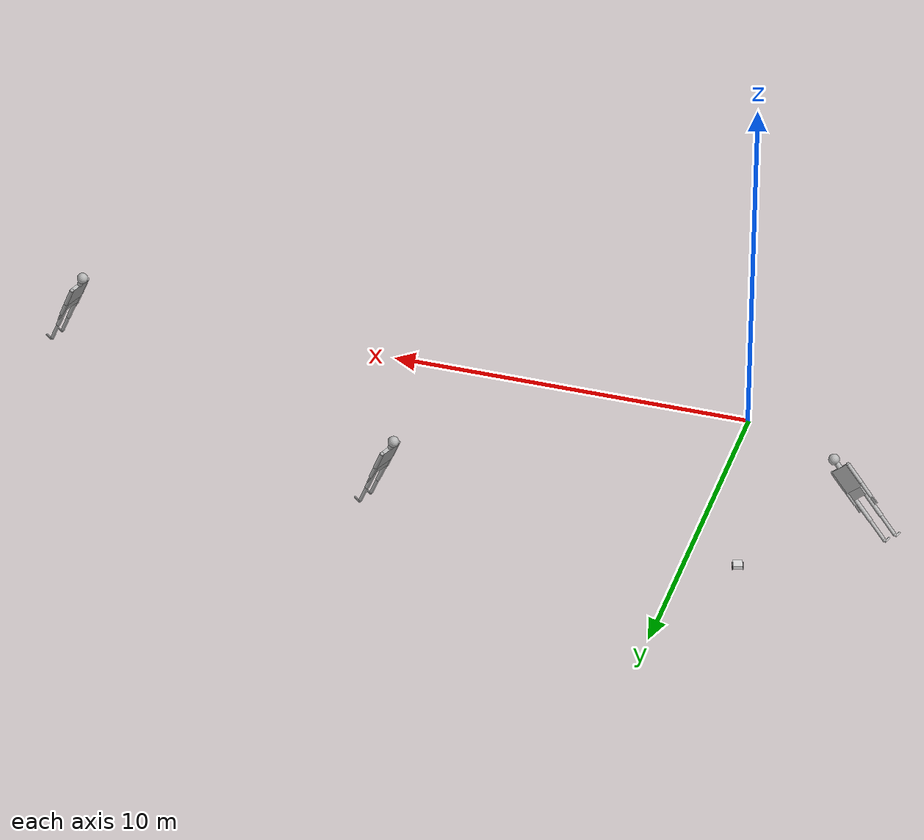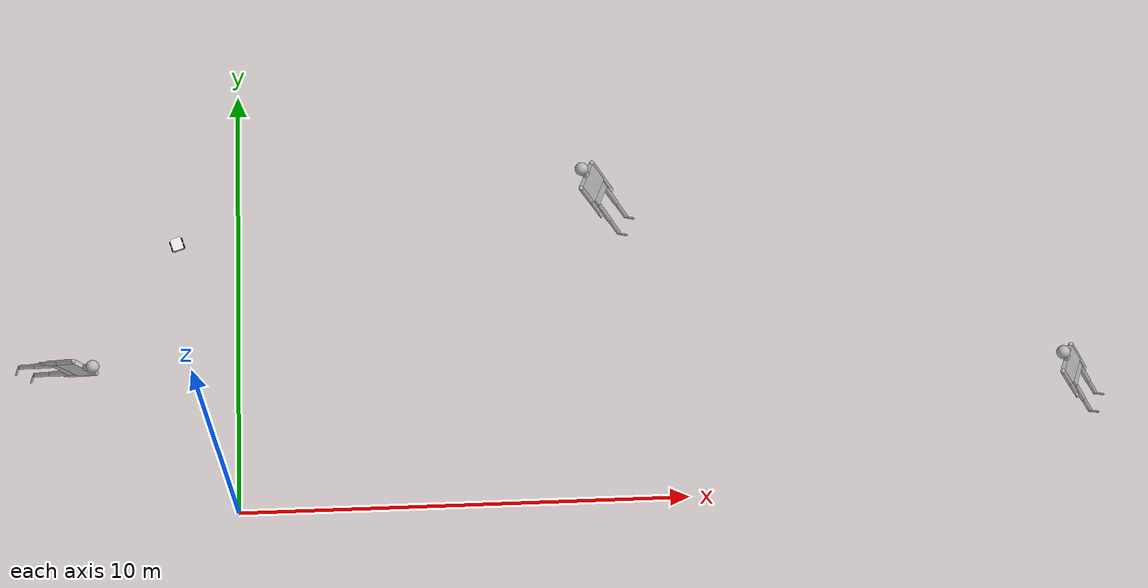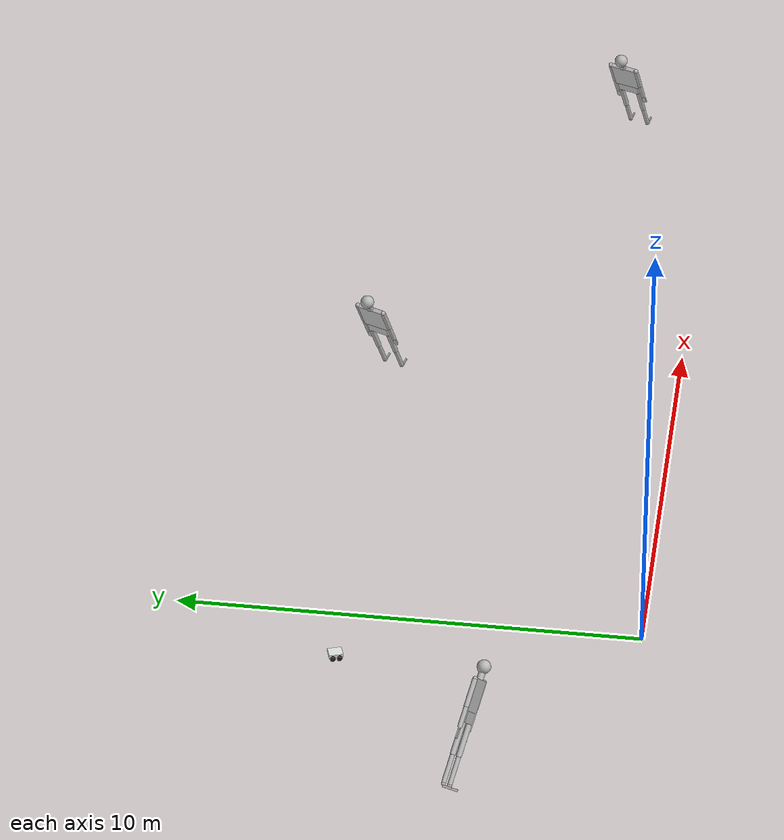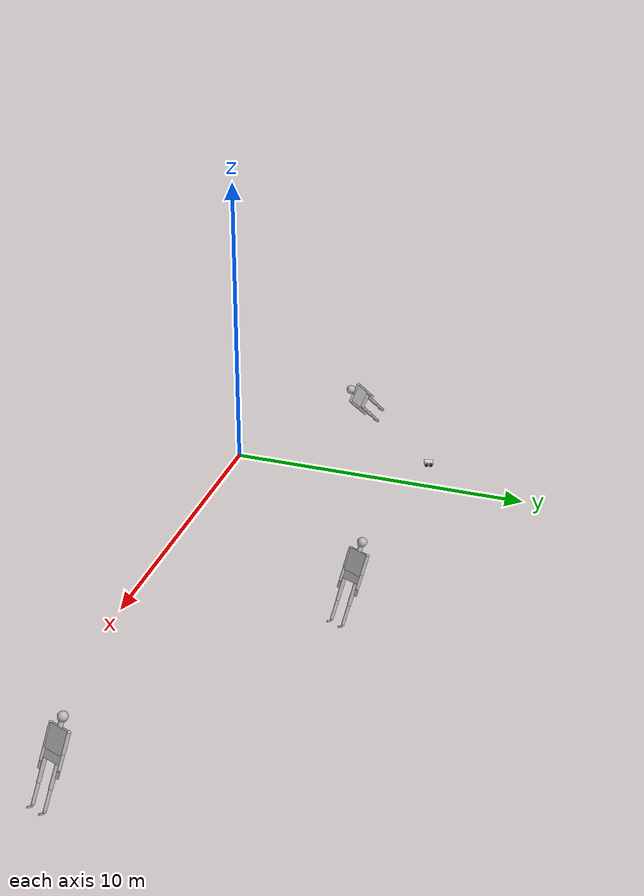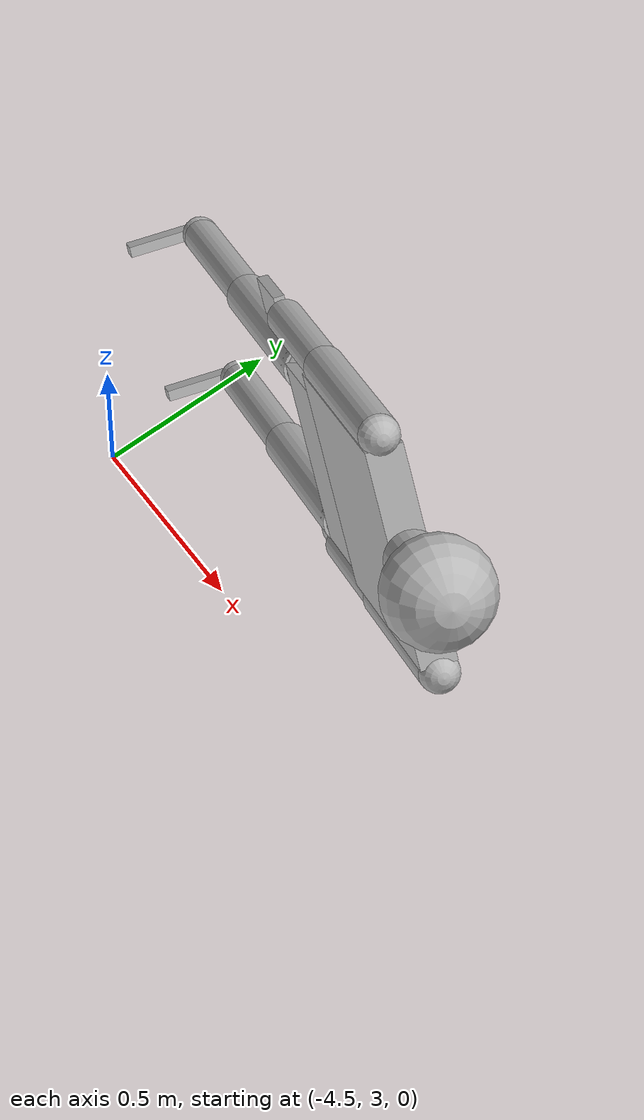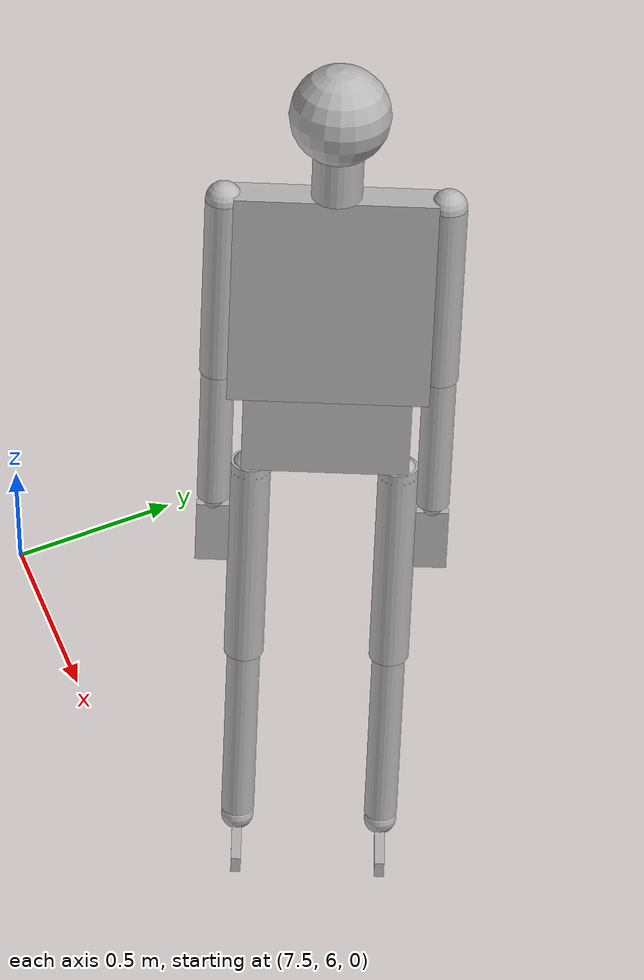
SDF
<sdf version="1.7">
 <world name="world_demo">
  <gravity>0 0 -9.8</gravity>
  <physics type="ode">
   <max_step_size>0.01</max_step_size>
   <real_time_factor>1</real_time_factor>
   <real_time_update_rate>1000</real_time_update_rate>
   <ode>
    <solver><type>quick</type><iters>50</iters><sor>1.3</sor></solver>
    <constraints><cfm>0</cfm><erp>0.2</erp></constraints>
   </ode>
  </physics>
  <plugin name="ignition::gazebo::systems::Physics" filename="libignition-gazebo-physics-system.so"/>
  <plugin name="ignition::gazebo::systems::UserCommands" filename="libignition-gazebo-user-commands-system.so"/>
  <plugin name="ignition::gazebo::systems::SceneBroadcaster" filename="libignition-gazebo-scene-broadcaster-system.so"/>
  <plugin name="ignition::gazebo::systems::Imu" filename="ignition-gazebo-imu-system"/>
  <plugin name="ignition::gazebo::systems::Sensors" filename="ignition-gazebo-sensors-system">
   <render_engine>ogre2</render_engine>
  </plugin>
  <scene>
   <ambient>1 1 1 1</ambient>
   <background>0.3 0.7 0.9 1</background>
   <shadows>0</shadows>
   <grid>0</grid>
  </scene>
  <magnetic_field>6e-06 2.3e-05 -4.2e-05</magnetic_field>
  <atmosphere type="adiabatic"/>
  <model name="ground_plane">
   <static>1</static>
   <link name="link">
    <collision name="collision">
     <geometry><plane><normal>0 0 1</normal><size>1 1</size></plane></geometry>
    </collision>
    <inertial>
     <mass>1</mass>
     <inertia><ixx>1</ixx><ixy>0</ixy><ixz>0</ixz><iyy>1</iyy><iyz>0</iyz><izz>1</izz></inertia>
    </inertial>
   </link>
  </model>
  <light name="sun" type="directional">
   <pose>-5 -3 10 0 -0 0</pose>
   <cast_shadows>0</cast_shadows>
   <direction>0 0 -1</direction>
   <diffuse>1 1 1 1</diffuse>
   <specular>1 1 1 1</specular>
   <attenuation><range>10</range><linear>1</linear><constant>1</constant><quadratic>0</quadratic></attenuation>
   <spot><inner_angle>0</inner_angle><outer_angle>0</outer_angle><falloff>0</falloff></spot>
   <intensity>1</intensity>
  </light>
  <audio><device>default</device></audio>
  <spherical_coordinates>
   <surface_model>EARTH_WGS84</surface_model>
   <latitude_deg>0</latitude_deg>
   <longitude_deg>0</longitude_deg>
   <elevation>0</elevation>
   <heading_deg>0</heading_deg>
  </spherical_coordinates>
  <model name="my_robot">
   <link name="base_footprint">
    <inertial>
     <pose>0.0375 0 0.0825 0 -0 0</pose>
     <mass>20</mass>
     <inertia>
      <ixx>0.297625</ixx>
      <ixy>0</ixy>
      <ixz>0.016875</ixz>
      <iyy>0.115083</iyy>
      <iyz>-1.16852e-18</iyz>
      <izz>0.360958</izz>
     </inertia>
    </inertial>
    <collision name="base_footprint_fixed_joint_lump__base_link_collision">
     <pose>0 0 0.105 0 -0 0</pose>
     <geometry><box><size>0.3 0.25 0.09</size></box></geometry>
    </collision>
    <collision name="base_footprint_fixed_joint_lump__left_camera_link_collision_1">
     <pose>0.1525 0.075 0.11 0 -0 0</pose>
     <geometry><box><size>0.005 0.05 0.03</size></box></geometry>
    </collision>
    <collision name="base_footprint_fixed_joint_lump__left_wheel_front_link_collision_2">
     <pose>0.075 0.14 0.06 1.5708 -0 0</pose>
     <geometry><cylinder><length>0.03</length><radius>0.06</radius></cylinder></geometry>
     <surface><friction><ode><mu>0</mu><mu2>0</mu2></ode></friction></surface>
    </collision>
    <collision name="base_footprint_fixed_joint_lump__right_camera_link_collision_3">
     <pose>0.1525 -0.075 0.11 0 -0 0</pose>
     <geometry><box><size>0.005 0.05 0.03</size></box></geometry>
    </collision>
    <collision name="base_footprint_fixed_joint_lump__right_wheel_front_link_collision_4">
     <pose>0.075 -0.14 0.06 1.5708 -0 0</pose>
     <geometry><cylinder><length>0.03</length><radius>0.06</radius></cylinder></geometry>
     <surface><friction><ode><mu>0</mu><mu2>0</mu2></ode></friction></surface>
    </collision>
    <visual name="base_footprint_fixed_joint_lump__base_link_visual">
     <pose>0 0 0.105 0 -0 0</pose>
     <geometry><box><size>0.3 0.25 0.09</size></box></geometry>
     <material>
      <script><name>Gazebo/White</name><uri>file://media/materials/scripts/gazebo.material</uri></script>
     </material>
    </visual>
    <visual name="base_footprint_fixed_joint_lump__left_camera_link_visual_1">
     <pose>0.1525 0.075 0.11 0 -0 0</pose>
     <geometry><box><size>0.005 0.05 0.03</size></box></geometry>
     <material>
      <script><name>Gazebo/Gold</name><uri>file://media/materials/scripts/gazebo.material</uri></script>
     </material>
    </visual>
    <visual name="base_footprint_fixed_joint_lump__left_wheel_front_link_visual_2">
     <pose>0.075 0.14 0.06 1.5708 -0 0</pose>
     <geometry><cylinder><length>0.03</length><radius>0.06</radius></cylinder></geometry>
     <material>
      <script><name>Gazebo/Black</name><uri>file://media/materials/scripts/gazebo.material</uri></script>
     </material>
    </visual>
    <visual name="base_footprint_fixed_joint_lump__right_camera_link_visual_3">
     <pose>0.1525 -0.075 0.11 0 -0 0</pose>
     <geometry><box><size>0.005 0.05 0.03</size></box></geometry>
     <material>
      <script><name>Gazebo/Gold</name><uri>file://media/materials/scripts/gazebo.material</uri></script>
     </material>
    </visual>
    <visual name="base_footprint_fixed_joint_lump__right_wheel_front_link_visual_4">
     <pose>0.075 -0.14 0.06 1.5708 -0 0</pose>
     <geometry><cylinder><length>0.03</length><radius>0.06</radius></cylinder></geometry>
     <material>
      <script><name>Gazebo/Black</name><uri>file://media/materials/scripts/gazebo.material</uri></script>
     </material>
    </visual>
    <sensor name="left_camera_sensor" type="camera">
     <visualize>1</visualize>
     <update_rate>15</update_rate>
     <camera>
      <horizontal_fov>2.0944</horizontal_fov>
      <image><width>752</width><height>480</height><format>R8G8B8</format></image>
      <clip><near>0.1</near><far>100</far></clip>
      <distortion><k1>0</k1><k2>0</k2><k3>0</k3><p1>0</p1><p2>0</p2><center>376.5 240.5</center></distortion>
      <intrinsics><fx>217.08247</fx><fy>217.08247</fy><cx>376.5</cx><cy>240.5</cy></intrinsics>
     </camera>
     <plugin name="left_camera_controller" filename="libgazebo_ros_camera.so">
      <frame_name>left_camera_optical_link</frame_name>
      <camera_name>left_camera</camera_name>
      <image_width>752</image_width>
      <image_height>480</image_height>
      <ros>
       <namespace>/camera/left</namespace>
       <remapping>image_raw:=image</remapping>
       <parameter name="publish_image">1</parameter>
       <parameter name="publish_compressed">0</parameter>
       <parameter name="publish_depth">0</parameter>
       <parameter name="disable_pub_plugins">["compressed", "compressedDepth", "theora"]</parameter>
      </ros>
     </plugin>
     <pose>0.1525 0.075 0.11 0 -0 0</pose>
    </sensor>
    <sensor name="right_camera_sensor" type="camera">
     <visualize>1</visualize>
     <update_rate>15</update_rate>
     <camera>
      <horizontal_fov>2.0944</horizontal_fov>
      <image><width>752</width><height>480</height><format>R8G8B8</format></image>
      <clip><near>0.1</near><far>100</far></clip>
      <distortion><k1>0</k1><k2>0</k2><k3>0</k3><p1>0</p1><p2>0</p2><center>376.5 240.5</center></distortion>
      <intrinsics><fx>217.08247</fx><fy>217.08247</fy><cx>376.5</cx><cy>240.5</cy></intrinsics>
     </camera>
     <plugin name="right_camera_controller" filename="libgazebo_ros_camera.so">
      <frame_name>right_camera_optical_link</frame_name>
      <camera_name>right_camera</camera_name>
      <image_width>752</image_width>
      <image_height>480</image_height>
      <ros>
       <namespace>/camera/right</namespace>
       <remapping>image_raw:=image</remapping>
       <parameter name="publish_image">1</parameter>
       <parameter name="publish_compressed">0</parameter>
       <parameter name="publish_depth">0</parameter>
       <parameter name="disable_pub_plugins">["compressed", "compressedDepth", "theora"]</parameter>
      </ros>
     </plugin>
     <pose>0.1525 -0.075 0.11 0 -0 0</pose>
    </sensor>
   </link>
   <joint name="base_left_wheel_back_joint" type="revolute">
    <pose relative_to="base_footprint">-0.075 0.14 0.06 0 -0 0</pose>
    <parent>base_footprint</parent>
    <child>left_wheel_back_link</child>
    <axis>
     <xyz>0 1 0</xyz>
     <limit><effort>10</effort><velocity>10</velocity><lower>-1e+16</lower><upper>1e+16</upper></limit>
     <dynamics><spring_reference>0</spring_reference><spring_stiffness>0</spring_stiffness></dynamics>
    </axis>
   </joint>
   <link name="left_wheel_back_link">
    <pose relative_to="base_left_wheel_back_joint">0 0 0 0 -0 0</pose>
    <inertial>
     <pose>0 0 0 1.5708 -0 0</pose>
     <mass>5</mass>
     <inertia><ixx>0.004875</ixx><ixy>0</ixy><ixz>0</ixz><iyy>0.004875</iyy><iyz>0</iyz><izz>0.009</izz></inertia>
    </inertial>
    <collision name="left_wheel_back_link_collision">
     <pose>0 0 0 1.5708 -0 0</pose>
     <geometry><cylinder><length>0.03</length><radius>0.06</radius></cylinder></geometry>
    </collision>
    <visual name="left_wheel_back_link_visual">
     <pose>0 0 0 1.5708 -0 0</pose>
     <geometry><cylinder><length>0.03</length><radius>0.06</radius></cylinder></geometry>
     <material>
      <script><name>Gazebo/Black</name><uri>file://media/materials/scripts/gazebo.material</uri></script>
     </material>
    </visual>
   </link>
   <joint name="base_right_wheel_back_joint" type="revolute">
    <pose relative_to="base_footprint">-0.075 -0.14 0.06 0 -0 0</pose>
    <parent>base_footprint</parent>
    <child>right_wheel_back_link</child>
    <axis>
     <xyz>0 1 0</xyz>
     <limit><effort>10</effort><velocity>10</velocity><lower>-1e+16</lower><upper>1e+16</upper></limit>
     <dynamics><spring_reference>0</spring_reference><spring_stiffness>0</spring_stiffness></dynamics>
    </axis>
   </joint>
   <link name="right_wheel_back_link">
    <pose relative_to="base_right_wheel_back_joint">0 0 0 0 -0 0</pose>
    <inertial>
     <pose>0 0 0 1.5708 -0 0</pose>
     <mass>5</mass>
     <inertia><ixx>0.004875</ixx><ixy>0</ixy><ixz>0</ixz><iyy>0.004875</iyy><iyz>0</iyz><izz>0.009</izz></inertia>
    </inertial>
    <collision name="right_wheel_back_link_collision">
     <pose>0 0 0 1.5708 -0 0</pose>
     <geometry><cylinder><length>0.03</length><radius>0.06</radius></cylinder></geometry>
    </collision>
    <visual name="right_wheel_back_link_visual">
     <pose>0 0 0 1.5708 -0 0</pose>
     <geometry><cylinder><length>0.03</length><radius>0.06</radius></cylinder></geometry>
     <material>
      <script><name>Gazebo/Black</name><uri>file://media/materials/scripts/gazebo.material</uri></script>
     </material>
    </visual>
   </link>
   <static>0</static>
   <plugin name="diff_drive_controller" filename="libgazebo_ros_diff_drive.so">
    <update_rate>50</update_rate>
    <left_joint>base_left_wheel_back_joint</left_joint>
    <right_joint>base_right_wheel_back_joint</right_joint>
    <wheel_separation>0.28</wheel_separation>
    <wheel_diameter>0.12</wheel_diameter>
    <publish_odom>1</publish_odom>
    <publish_odom_tf>1</publish_odom_tf>
    <publish_wheel_tf>1</publish_wheel_tf>
    <odometry_topic>odom</odometry_topic>
    <odometry_frame>odom</odometry_frame>
    <robot_base_frame>base_footprint</robot_base_frame>
    <ros><namespace>/</namespace><remapping>cmd_vel:=cmd_vel</remapping><remapping>odom:=odom</remapping></ros>
    <max_wheel_torque>200</max_wheel_torque>
    <max_wheel_acceleration>10.0</max_wheel_acceleration>
    <command_topic>cmd_vel</command_topic>
   </plugin>
   <pose>-1.40323 6.37927 1.1e-05 2.6e-05 7.2e-05 -1.26523</pose>
  </model>
  <model name="ragdoll">
   <pose>8.30716 6.70939 1.38123 -0.028547 -0.41916 -0.39293</pose>
   <link name="hip">
    <inertial>
     <inertia><ixx>0.1</ixx><ixy>0</ixy><ixz>0</ixz><iyy>0.1</iyy><iyz>0</iyz><izz>0.1</izz></inertia>
     <mass>10</mass>
    </inertial>
    <collision name="hip_geom">
     <pose>0 0 0.125 0 -0 0</pose>
     <geometry><box><size>0.1 0.5 0.25</size></box></geometry>
     <surface>
      <friction><ode><mu>-1</mu><mu2>-1</mu2><fdir1>0 0 0</fdir1><slip1>0</slip1><slip2>0</slip2></ode></friction>
      <bounce><restitution_coefficient>0</restitution_coefficient><threshold>100000</threshold></bounce>
      <contact>
       <ode>
        <soft_cfm>0</soft_cfm>
        <soft_erp>0.2</soft_erp>
        <kp>1e+12</kp>
        <kd>1</kd>
        <max_vel>0</max_vel>
        <min_depth>0.001</min_depth>
       </ode>
      </contact>
     </surface>
    </collision>
    <visual name="hip_geom_visual">
     <pose>0 0 0.125 0 -0 0</pose>
     <geometry><box><size>0.1 0.5 0.25</size></box></geometry>
    </visual>
    <gravity>0</gravity>
   </link>
   <link name="l_thigh_pan">
    <pose>0 0.22 0 0 -0 0</pose>
    <inertial>
     <inertia><ixx>0.01</ixx><ixy>0</ixy><ixz>0</ixz><iyy>0.01</iyy><iyz>0</iyz><izz>0.01</izz></inertia>
     <mass>1</mass>
    </inertial>
    <collision name="l_thigh_pan_geom">
     <pose>0 0 -0.03 0 -0 0</pose>
     <geometry><sphere><radius>0.06</radius></sphere></geometry>
     <surface>
      <friction><ode><mu>-1</mu><mu2>-1</mu2><fdir1>0 0 0</fdir1><slip1>0</slip1><slip2>0</slip2></ode></friction>
      <bounce><restitution_coefficient>0</restitution_coefficient><threshold>100000</threshold></bounce>
      <contact>
       <ode>
        <soft_cfm>0</soft_cfm>
        <soft_erp>0.2</soft_erp>
        <kp>1e+12</kp>
        <kd>1</kd>
        <max_vel>0</max_vel>
        <min_depth>0.001</min_depth>
       </ode>
      </contact>
     </surface>
    </collision>
    <visual name="l_thigh_pan_geom_visual">
     <pose>0 0 -0.03 0 -0 0</pose>
     <geometry><sphere><radius>0.06</radius></sphere></geometry>
    </visual>
    <gravity>0</gravity>
   </link>
   <link name="l_thigh_lift">
    <pose>0 0.22 0 0 -0 0</pose>
    <inertial>
     <inertia><ixx>0.05</ixx><ixy>0</ixy><ixz>0</ixz><iyy>0.05</iyy><iyz>0</iyz><izz>0.05</izz></inertia>
     <mass>5</mass>
    </inertial>
    <collision name="l_thigh_lift_geom">
     <pose>0 0 -0.35 0 -0 0</pose>
     <geometry><cylinder><radius>0.06</radius><length>0.7</length></cylinder></geometry>
     <surface>
      <friction><ode><mu>-1</mu><mu2>-1</mu2><fdir1>0 0 0</fdir1><slip1>0</slip1><slip2>0</slip2></ode></friction>
      <bounce><restitution_coefficient>0</restitution_coefficient><threshold>100000</threshold></bounce>
      <contact>
       <ode>
        <soft_cfm>0</soft_cfm>
        <soft_erp>0.2</soft_erp>
        <kp>1e+12</kp>
        <kd>1</kd>
        <max_vel>0</max_vel>
        <min_depth>0.001</min_depth>
       </ode>
      </contact>
     </surface>
    </collision>
    <visual name="l_thigh_lift_geom_visual">
     <pose>0 0 -0.35 0 -0 0</pose>
     <geometry><cylinder><radius>0.06</radius><length>0.7</length></cylinder></geometry>
    </visual>
    <gravity>0</gravity>
   </link>
   <link name="l_calf">
    <pose>0 0.22 -0.7 0 -0 0</pose>
    <inertial>
     <inertia><ixx>0.02</ixx><ixy>0</ixy><ixz>0</ixz><iyy>0.02</iyy><iyz>0</iyz><izz>0.02</izz></inertia>
     <mass>2</mass>
    </inertial>
    <collision name="l_calf_geom">
     <pose>0 0 -0.3 0 -0 0</pose>
     <geometry><cylinder><radius>0.05</radius><length>0.6</length></cylinder></geometry>
     <surface>
      <friction><ode><mu>-1</mu><mu2>-1</mu2><fdir1>0 0 0</fdir1><slip1>0</slip1><slip2>0</slip2></ode></friction>
      <bounce><restitution_coefficient>0</restitution_coefficient><threshold>100000</threshold></bounce>
      <contact>
       <ode>
        <soft_cfm>0</soft_cfm>
        <soft_erp>0.2</soft_erp>
        <kp>1e+12</kp>
        <kd>1</kd>
        <max_vel>0</max_vel>
        <min_depth>0.001</min_depth>
       </ode>
      </contact>
     </surface>
    </collision>
    <visual name="l_calf_geom_visual">
     <pose>0 0 -0.3 0 -0 0</pose>
     <geometry><cylinder><radius>0.05</radius><length>0.6</length></cylinder></geometry>
    </visual>
    <gravity>0</gravity>
   </link>
   <link name="l_ankle">
    <pose>0 0.22 -1.325 0 -0 0</pose>
    <inertial>
     <inertia><ixx>0.01</ixx><ixy>0</ixy><ixz>0</ixz><iyy>0.01</iyy><iyz>0</iyz><izz>0.01</izz></inertia>
     <mass>1</mass>
    </inertial>
    <collision name="l_ankle_geom">
     <geometry><sphere><radius>0.05</radius></sphere></geometry>
     <surface>
      <friction><ode><mu>-1</mu><mu2>-1</mu2><fdir1>0 0 0</fdir1><slip1>0</slip1><slip2>0</slip2></ode></friction>
      <bounce><restitution_coefficient>0</restitution_coefficient><threshold>100000</threshold></bounce>
      <contact>
       <ode>
        <soft_cfm>0</soft_cfm>
        <soft_erp>0.2</soft_erp>
        <kp>1e+12</kp>
        <kd>1</kd>
        <max_vel>0</max_vel>
        <min_depth>0.001</min_depth>
       </ode>
      </contact>
     </surface>
    </collision>
    <visual name="l_ankle_geom_visual"><geometry><sphere><radius>0.05</radius></sphere></geometry></visual>
    <gravity>0</gravity>
   </link>
   <link name="l_foot">
    <pose>0 0.22 -1.35 0 -0 0</pose>
    <inertial>
     <pose>0.1 0 0 0 -0 0</pose>
     <inertia><ixx>0.01</ixx><ixy>0</ixy><ixz>0</ixz><iyy>0.01</iyy><iyz>0</iyz><izz>0.01</izz></inertia>
     <mass>1</mass>
    </inertial>
    <collision name="l_foot_geom">
     <pose>0.1 0 -0.025 0 -0 0</pose>
     <geometry><box><size>0.2 0.03 0.05</size></box></geometry>
     <surface>
      <friction><ode><mu>-1</mu><mu2>-1</mu2><fdir1>0 0 0</fdir1><slip1>0</slip1><slip2>0</slip2></ode></friction>
      <bounce><restitution_coefficient>0</restitution_coefficient><threshold>100000</threshold></bounce>
      <contact>
       <ode>
        <soft_cfm>0</soft_cfm>
        <soft_erp>0.2</soft_erp>
        <kp>1e+12</kp>
        <kd>1</kd>
        <max_vel>0</max_vel>
        <min_depth>0.001</min_depth>
       </ode>
      </contact>
     </surface>
    </collision>
    <visual name="l_foot_geom_visual">
     <pose>0.1 0 -0.025 0 -0 0</pose>
     <geometry><box><size>0.2 0.03 0.05</size></box></geometry>
    </visual>
   </link>
   <link name="r_thigh_pan">
    <pose>0 -0.22 0 0 -0 0</pose>
    <inertial>
     <inertia><ixx>0.01</ixx><ixy>0</ixy><ixz>0</ixz><iyy>0.01</iyy><iyz>0</iyz><izz>0.01</izz></inertia>
     <mass>1</mass>
    </inertial>
    <collision name="r_thigh_pan_geom">
     <pose>0 0 -0.03 0 -0 0</pose>
     <geometry><sphere><radius>0.06</radius></sphere></geometry>
     <surface>
      <friction><ode><mu>-1</mu><mu2>-1</mu2><fdir1>0 0 0</fdir1><slip1>0</slip1><slip2>0</slip2></ode></friction>
      <bounce><restitution_coefficient>0</restitution_coefficient><threshold>100000</threshold></bounce>
      <contact>
       <ode>
        <soft_cfm>0</soft_cfm>
        <soft_erp>0.2</soft_erp>
        <kp>1e+12</kp>
        <kd>1</kd>
        <max_vel>0</max_vel>
        <min_depth>0.001</min_depth>
       </ode>
      </contact>
     </surface>
    </collision>
    <visual name="r_thigh_pan_geom_visual">
     <pose>0 0 -0.03 0 -0 0</pose>
     <geometry><sphere><radius>0.06</radius></sphere></geometry>
    </visual>
    <gravity>0</gravity>
   </link>
   <link name="r_thigh_lift">
    <pose>0 -0.22 0 0 -0 0</pose>
    <inertial>
     <inertia><ixx>0.05</ixx><ixy>0</ixy><ixz>0</ixz><iyy>0.05</iyy><iyz>0</iyz><izz>0.05</izz></inertia>
     <mass>5</mass>
    </inertial>
    <collision name="r_thigh_lift_geom">
     <pose>0 0 -0.35 0 -0 0</pose>
     <geometry><cylinder><radius>0.06</radius><length>0.7</length></cylinder></geometry>
     <surface>
      <friction><ode><mu>-1</mu><mu2>-1</mu2><fdir1>0 0 0</fdir1><slip1>0</slip1><slip2>0</slip2></ode></friction>
      <bounce><restitution_coefficient>0</restitution_coefficient><threshold>100000</threshold></bounce>
      <contact>
       <ode>
        <soft_cfm>0</soft_cfm>
        <soft_erp>0.2</soft_erp>
        <kp>1e+12</kp>
        <kd>1</kd>
        <max_vel>0</max_vel>
        <min_depth>0.001</min_depth>
       </ode>
      </contact>
     </surface>
    </collision>
    <visual name="r_thigh_lift_geom_visual">
     <pose>0 0 -0.35 0 -0 0</pose>
     <geometry><cylinder><radius>0.06</radius><length>0.7</length></cylinder></geometry>
    </visual>
    <gravity>0</gravity>
   </link>
   <link name="r_calf">
    <pose>0 -0.22 -0.7 0 -0 0</pose>
    <inertial>
     <inertia><ixx>0.02</ixx><ixy>0</ixy><ixz>0</ixz><iyy>0.02</iyy><iyz>0</iyz><izz>0.02</izz></inertia>
     <mass>2</mass>
    </inertial>
    <collision name="r_calf_geom">
     <pose>0 0 -0.3 0 -0 0</pose>
     <geometry><cylinder><radius>0.05</radius><length>0.6</length></cylinder></geometry>
     <surface>
      <friction><ode><mu>-1</mu><mu2>-1</mu2><fdir1>0 0 0</fdir1><slip1>0</slip1><slip2>0</slip2></ode></friction>
      <bounce><restitution_coefficient>0</restitution_coefficient><threshold>100000</threshold></bounce>
      <contact>
       <ode>
        <soft_cfm>0</soft_cfm>
        <soft_erp>0.2</soft_erp>
        <kp>1e+12</kp>
        <kd>1</kd>
        <max_vel>0</max_vel>
        <min_depth>0.001</min_depth>
       </ode>
      </contact>
     </surface>
    </collision>
    <visual name="r_calf_geom_visual">
     <pose>0 0 -0.3 0 -0 0</pose>
     <geometry><cylinder><radius>0.05</radius><length>0.6</length></cylinder></geometry>
    </visual>
    <gravity>0</gravity>
   </link>
   <link name="r_ankle">
    <pose>0 -0.22 -1.325 0 -0 0</pose>
    <inertial>
     <inertia><ixx>0.01</ixx><ixy>0</ixy><ixz>0</ixz><iyy>0.01</iyy><iyz>0</iyz><izz>0.01</izz></inertia>
     <mass>1</mass>
    </inertial>
    <collision name="r_ankle_geom">
     <geometry><sphere><radius>0.05</radius></sphere></geometry>
     <surface>
      <friction><ode><mu>-1</mu><mu2>-1</mu2><fdir1>0 0 0</fdir1><slip1>0</slip1><slip2>0</slip2></ode></friction>
      <bounce><restitution_coefficient>0</restitution_coefficient><threshold>100000</threshold></bounce>
      <contact>
       <ode>
        <soft_cfm>0</soft_cfm>
        <soft_erp>0.2</soft_erp>
        <kp>1e+12</kp>
        <kd>1</kd>
        <max_vel>0</max_vel>
        <min_depth>0.001</min_depth>
       </ode>
      </contact>
     </surface>
    </collision>
    <visual name="r_ankle_geom_visual"><geometry><sphere><radius>0.05</radius></sphere></geometry></visual>
    <gravity>0</gravity>
   </link>
   <link name="r_foot">
    <pose>0 -0.22 -1.35 0 -0 0</pose>
    <inertial>
     <pose>0.1 0 0 0 -0 0</pose>
     <inertia><ixx>0.01</ixx><ixy>0</ixy><ixz>0</ixz><iyy>0.01</iyy><iyz>0</iyz><izz>0.01</izz></inertia>
     <mass>1</mass>
    </inertial>
    <collision name="r_foot_geom">
     <pose>0.1 0 -0.025 0 -0 0</pose>
     <geometry><box><size>0.2 0.03 0.05</size></box></geometry>
     <surface>
      <friction><ode><mu>-1</mu><mu2>-1</mu2><fdir1>0 0 0</fdir1><slip1>0</slip1><slip2>0</slip2></ode></friction>
      <bounce><restitution_coefficient>0</restitution_coefficient><threshold>100000</threshold></bounce>
      <contact>
       <ode>
        <soft_cfm>0</soft_cfm>
        <soft_erp>0.2</soft_erp>
        <kp>1e+12</kp>
        <kd>1</kd>
        <max_vel>0</max_vel>
        <min_depth>0.001</min_depth>
       </ode>
      </contact>
     </surface>
    </collision>
    <visual name="r_foot_geom_visual">
     <pose>0.1 0 -0.025 0 -0 0</pose>
     <geometry><box><size>0.2 0.03 0.05</size></box></geometry>
    </visual>
   </link>
   <link name="torso">
    <pose>0 0 0.25 0 -0 0</pose>
    <inertial>
     <inertia><ixx>0.3</ixx><ixy>0</ixy><ixz>0</ixz><iyy>0.3</iyy><iyz>0</iyz><izz>0.3</izz></inertia>
     <mass>30</mass>
    </inertial>
    <collision name="torso_geom">
     <pose>0 0 0.35 0 -0 0</pose>
     <geometry><box><size>0.1 0.6 0.7</size></box></geometry>
     <surface>
      <friction><ode><mu>-1</mu><mu2>-1</mu2><fdir1>0 0 0</fdir1><slip1>0</slip1><slip2>0</slip2></ode></friction>
      <bounce><restitution_coefficient>0</restitution_coefficient><threshold>100000</threshold></bounce>
      <contact>
       <ode>
        <soft_cfm>0</soft_cfm>
        <soft_erp>0.2</soft_erp>
        <kp>1e+12</kp>
        <kd>1</kd>
        <max_vel>0</max_vel>
        <min_depth>0.001</min_depth>
       </ode>
      </contact>
     </surface>
    </collision>
    <visual name="torso_geom_visual">
     <pose>0 0 0.35 0 -0 0</pose>
     <geometry><box><size>0.1 0.6 0.7</size></box></geometry>
    </visual>
    <gravity>0</gravity>
   </link>
   <link name="l_shoulder">
    <pose>0 0.3275 0.9225 0 -0 0</pose>
    <inertial>
     <inertia><ixx>0.01</ixx><ixy>0</ixy><ixz>0</ixz><iyy>0.01</iyy><iyz>0</iyz><izz>0.01</izz></inertia>
     <mass>1</mass>
    </inertial>
    <collision name="l_shoulder_geom">
     <geometry><sphere><radius>0.055</radius></sphere></geometry>
     <surface>
      <friction><ode><mu>-1</mu><mu2>-1</mu2><fdir1>0 0 0</fdir1><slip1>0</slip1><slip2>0</slip2></ode></friction>
      <bounce><restitution_coefficient>0</restitution_coefficient><threshold>100000</threshold></bounce>
      <contact>
       <ode>
        <soft_cfm>0</soft_cfm>
        <soft_erp>0.2</soft_erp>
        <kp>1e+12</kp>
        <kd>1</kd>
        <max_vel>0</max_vel>
        <min_depth>0.001</min_depth>
       </ode>
      </contact>
     </surface>
    </collision>
    <visual name="l_shoulder_geom_visual"><geometry><sphere><radius>0.055</radius></sphere></geometry></visual>
    <gravity>0</gravity>
   </link>
   <link name="l_upper_arm">
    <pose>0 0.3275 0.9225 0 -0 0</pose>
    <inertial>
     <inertia><ixx>0.02</ixx><ixy>0</ixy><ixz>0</ixz><iyy>0.02</iyy><iyz>0</iyz><izz>0.02</izz></inertia>
     <mass>2</mass>
    </inertial>
    <collision name="l_upper_arm_geom">
     <pose>0 0 -0.3 0 -0 0</pose>
     <geometry><cylinder><radius>0.055</radius><length>0.6</length></cylinder></geometry>
     <surface>
      <friction><ode><mu>-1</mu><mu2>-1</mu2><fdir1>0 0 0</fdir1><slip1>0</slip1><slip2>0</slip2></ode></friction>
      <bounce><restitution_coefficient>0</restitution_coefficient><threshold>100000</threshold></bounce>
      <contact>
       <ode>
        <soft_cfm>0</soft_cfm>
        <soft_erp>0.2</soft_erp>
        <kp>1e+12</kp>
        <kd>1</kd>
        <max_vel>0</max_vel>
        <min_depth>0.001</min_depth>
       </ode>
      </contact>
     </surface>
    </collision>
    <visual name="l_upper_arm_geom_visual">
     <pose>0 0 -0.3 0 -0 0</pose>
     <geometry><cylinder><radius>0.055</radius><length>0.6</length></cylinder></geometry>
    </visual>
    <gravity>0</gravity>
   </link>
   <link name="l_forearm">
    <pose>0 0.3275 0.3225 0 -0 0</pose>
    <inertial>
     <inertia><ixx>0.01</ixx><ixy>0</ixy><ixz>0</ixz><iyy>0.01</iyy><iyz>0</iyz><izz>0.01</izz></inertia>
     <mass>1</mass>
    </inertial>
    <collision name="l_forearm_geom">
     <pose>0 0 -0.225 0 -0 0</pose>
     <geometry><cylinder><radius>0.05</radius><length>0.45</length></cylinder></geometry>
     <surface>
      <friction><ode><mu>-1</mu><mu2>-1</mu2><fdir1>0 0 0</fdir1><slip1>0</slip1><slip2>0</slip2></ode></friction>
      <bounce><restitution_coefficient>0</restitution_coefficient><threshold>100000</threshold></bounce>
      <contact>
       <ode>
        <soft_cfm>0</soft_cfm>
        <soft_erp>0.2</soft_erp>
        <kp>1e+12</kp>
        <kd>1</kd>
        <max_vel>0</max_vel>
        <min_depth>0.001</min_depth>
       </ode>
      </contact>
     </surface>
    </collision>
    <visual name="l_forearm_geom_visual">
     <pose>0 0 -0.225 0 -0 0</pose>
     <geometry><cylinder><radius>0.05</radius><length>0.45</length></cylinder></geometry>
    </visual>
    <gravity>0</gravity>
   </link>
   <link name="l_wrist">
    <pose>0 0.3275 -0.1425 0 -0 0</pose>
    <inertial>
     <inertia><ixx>0.01</ixx><ixy>0</ixy><ixz>0</ixz><iyy>0.01</iyy><iyz>0</iyz><izz>0.01</izz></inertia>
     <mass>1</mass>
    </inertial>
    <collision name="l_wrist_geom">
     <geometry><sphere><radius>0.03</radius></sphere></geometry>
     <surface>
      <friction><ode><mu>-1</mu><mu2>-1</mu2><fdir1>0 0 0</fdir1><slip1>0</slip1><slip2>0</slip2></ode></friction>
      <bounce><restitution_coefficient>0</restitution_coefficient><threshold>100000</threshold></bounce>
      <contact>
       <ode>
        <soft_cfm>0</soft_cfm>
        <soft_erp>0.2</soft_erp>
        <kp>1e+12</kp>
        <kd>1</kd>
        <max_vel>0</max_vel>
        <min_depth>0.001</min_depth>
       </ode>
      </contact>
     </surface>
    </collision>
    <visual name="l_wrist_geom_visual"><geometry><sphere><radius>0.03</radius></sphere></geometry></visual>
    <gravity>0</gravity>
   </link>
   <link name="l_hand">
    <pose>0 0.3275 -0.1575 0 -0 0</pose>
    <inertial>
     <inertia><ixx>0.01</ixx><ixy>0</ixy><ixz>0</ixz><iyy>0.01</iyy><iyz>0</iyz><izz>0.01</izz></inertia>
     <mass>1</mass>
    </inertial>
    <collision name="l_hand_geom">
     <pose>0 0 -0.1 0 -0 0</pose>
     <geometry><box><size>0.03 0.1 0.2</size></box></geometry>
     <surface>
      <friction><ode><mu>-1</mu><mu2>-1</mu2><fdir1>0 0 0</fdir1><slip1>0</slip1><slip2>0</slip2></ode></friction>
      <bounce><restitution_coefficient>0</restitution_coefficient><threshold>100000</threshold></bounce>
      <contact>
       <ode>
        <soft_cfm>0</soft_cfm>
        <soft_erp>0.2</soft_erp>
        <kp>1e+12</kp>
        <kd>1</kd>
        <max_vel>0</max_vel>
        <min_depth>0.001</min_depth>
       </ode>
      </contact>
     </surface>
    </collision>
    <visual name="l_hand_geom_visual">
     <pose>0 0 -0.1 0 -0 0</pose>
     <geometry><box><size>0.03 0.1 0.2</size></box></geometry>
    </visual>
    <gravity>0</gravity>
   </link>
   <link name="neck">
    <pose>0 0 0.95 0 -0 0</pose>
    <inertial>
     <inertia><ixx>0.01</ixx><ixy>0</ixy><ixz>0</ixz><iyy>0.01</iyy><iyz>0</iyz><izz>0.01</izz></inertia>
     <mass>1</mass>
    </inertial>
    <collision name="neck_geom">
     <pose>0 0 0.1 0 -0 0</pose>
     <geometry><cylinder><radius>0.075</radius><length>0.2</length></cylinder></geometry>
     <surface>
      <friction><ode><mu>-1</mu><mu2>-1</mu2><fdir1>0 0 0</fdir1><slip1>0</slip1><slip2>0</slip2></ode></friction>
      <bounce><restitution_coefficient>0</restitution_coefficient><threshold>100000</threshold></bounce>
      <contact>
       <ode>
        <soft_cfm>0</soft_cfm>
        <soft_erp>0.2</soft_erp>
        <kp>1e+12</kp>
        <kd>1</kd>
        <max_vel>0</max_vel>
        <min_depth>0.001</min_depth>
       </ode>
      </contact>
     </surface>
    </collision>
    <visual name="neck_geom_visual">
     <pose>0 0 0.1 0 -0 0</pose>
     <geometry><cylinder><radius>0.075</radius><length>0.2</length></cylinder></geometry>
    </visual>
    <gravity>0</gravity>
   </link>
   <link name="head">
    <pose>0 0 1.225 0 -0 0</pose>
    <inertial>
     <inertia><ixx>0.1</ixx><ixy>0</ixy><ixz>0</ixz><iyy>0.1</iyy><iyz>0</iyz><izz>0.1</izz></inertia>
     <mass>10</mass>
    </inertial>
    <collision name="head_geom">
     <geometry><sphere><radius>0.15</radius></sphere></geometry>
     <surface>
      <friction><ode><mu>-1</mu><mu2>-1</mu2><fdir1>0 0 0</fdir1><slip1>0</slip1><slip2>0</slip2></ode></friction>
      <bounce><restitution_coefficient>0</restitution_coefficient><threshold>100000</threshold></bounce>
      <contact>
       <ode>
        <soft_cfm>0</soft_cfm>
        <soft_erp>0.2</soft_erp>
        <kp>1e+12</kp>
        <kd>1</kd>
        <max_vel>0</max_vel>
        <min_depth>0.001</min_depth>
       </ode>
      </contact>
     </surface>
    </collision>
    <visual name="head_geom_visual"><geometry><sphere><radius>0.15</radius></sphere></geometry></visual>
    <gravity>0</gravity>
   </link>
   <link name="r_shoulder">
    <pose>0 -0.3275 0.9225 0 -0 0</pose>
    <inertial>
     <inertia><ixx>0.01</ixx><ixy>0</ixy><ixz>0</ixz><iyy>0.01</iyy><iyz>0</iyz><izz>0.01</izz></inertia>
     <mass>1</mass>
    </inertial>
    <collision name="r_shoulder_geom">
     <geometry><sphere><radius>0.055</radius></sphere></geometry>
     <surface>
      <friction><ode><mu>-1</mu><mu2>-1</mu2><fdir1>0 0 0</fdir1><slip1>0</slip1><slip2>0</slip2></ode></friction>
      <bounce><restitution_coefficient>0</restitution_coefficient><threshold>100000</threshold></bounce>
      <contact>
       <ode>
        <soft_cfm>0</soft_cfm>
        <soft_erp>0.2</soft_erp>
        <kp>1e+12</kp>
        <kd>1</kd>
        <max_vel>0</max_vel>
        <min_depth>0.001</min_depth>
       </ode>
      </contact>
     </surface>
    </collision>
    <visual name="r_shoulder_geom_visual"><geometry><sphere><radius>0.055</radius></sphere></geometry></visual>
    <gravity>0</gravity>
   </link>
   <link name="r_upper_arm">
    <pose>0 -0.3275 0.9225 0 -0 0</pose>
    <inertial>
     <inertia><ixx>0.02</ixx><ixy>0</ixy><ixz>0</ixz><iyy>0.02</iyy><iyz>0</iyz><izz>0.02</izz></inertia>
     <mass>2</mass>
    </inertial>
    <collision name="r_upper_arm_geom">
     <pose>0 0 -0.3 0 -0 0</pose>
     <geometry><cylinder><radius>0.055</radius><length>0.6</length></cylinder></geometry>
     <surface>
      <friction><ode><mu>-1</mu><mu2>-1</mu2><fdir1>0 0 0</fdir1><slip1>0</slip1><slip2>0</slip2></ode></friction>
      <bounce><restitution_coefficient>0</restitution_coefficient><threshold>100000</threshold></bounce>
      <contact>
       <ode>
        <soft_cfm>0</soft_cfm>
        <soft_erp>0.2</soft_erp>
        <kp>1e+12</kp>
        <kd>1</kd>
        <max_vel>0</max_vel>
        <min_depth>0.001</min_depth>
       </ode>
      </contact>
     </surface>
    </collision>
    <visual name="r_upper_arm_geom_visual">
     <pose>0 0 -0.3 0 -0 0</pose>
     <geometry><cylinder><radius>0.055</radius><length>0.6</length></cylinder></geometry>
    </visual>
    <gravity>0</gravity>
   </link>
   <link name="r_forearm">
    <pose>0 -0.3275 0.3225 0 -0 0</pose>
    <inertial>
     <inertia><ixx>0.01</ixx><ixy>0</ixy><ixz>0</ixz><iyy>0.01</iyy><iyz>0</iyz><izz>0.01</izz></inertia>
     <mass>1</mass>
    </inertial>
    <collision name="r_forearm_geom">
     <pose>0 0 -0.225 0 -0 0</pose>
     <geometry><cylinder><radius>0.05</radius><length>0.45</length></cylinder></geometry>
     <surface>
      <friction><ode><mu>-1</mu><mu2>-1</mu2><fdir1>0 0 0</fdir1><slip1>0</slip1><slip2>0</slip2></ode></friction>
      <bounce><restitution_coefficient>0</restitution_coefficient><threshold>100000</threshold></bounce>
      <contact>
       <ode>
        <soft_cfm>0</soft_cfm>
        <soft_erp>0.2</soft_erp>
        <kp>1e+12</kp>
        <kd>1</kd>
        <max_vel>0</max_vel>
        <min_depth>0.001</min_depth>
       </ode>
      </contact>
     </surface>
    </collision>
    <visual name="r_forearm_geom_visual">
     <pose>0 0 -0.225 0 -0 0</pose>
     <geometry><cylinder><radius>0.05</radius><length>0.45</length></cylinder></geometry>
    </visual>
    <gravity>0</gravity>
   </link>
   <link name="r_wrist">
    <pose>0 -0.3275 -0.1425 0 -0 0</pose>
    <inertial>
     <inertia><ixx>0.01</ixx><ixy>0</ixy><ixz>0</ixz><iyy>0.01</iyy><iyz>0</iyz><izz>0.01</izz></inertia>
     <mass>1</mass>
    </inertial>
    <collision name="r_wrist_geom">
     <geometry><sphere><radius>0.03</radius></sphere></geometry>
     <surface>
      <friction><ode><mu>-1</mu><mu2>-1</mu2><fdir1>0 0 0</fdir1><slip1>0</slip1><slip2>0</slip2></ode></friction>
      <bounce><restitution_coefficient>0</restitution_coefficient><threshold>100000</threshold></bounce>
      <contact>
       <ode>
        <soft_cfm>0</soft_cfm>
        <soft_erp>0.2</soft_erp>
        <kp>1e+12</kp>
        <kd>1</kd>
        <max_vel>0</max_vel>
        <min_depth>0.001</min_depth>
       </ode>
      </contact>
     </surface>
    </collision>
    <visual name="r_wrist_geom_visual"><geometry><sphere><radius>0.03</radius></sphere></geometry></visual>
    <gravity>0</gravity>
   </link>
   <link name="r_hand">
    <pose>0 -0.3275 -0.1575 0 -0 0</pose>
    <inertial>
     <inertia><ixx>0.01</ixx><ixy>0</ixy><ixz>0</ixz><iyy>0.01</iyy><iyz>0</iyz><izz>0.01</izz></inertia>
     <mass>1</mass>
    </inertial>
    <collision name="r_hand_geom">
     <pose>0 0 -0.1 0 -0 0</pose>
     <geometry><box><size>0.03 0.1 0.2</size></box></geometry>
     <surface>
      <friction><ode><mu>-1</mu><mu2>-1</mu2><fdir1>0 0 0</fdir1><slip1>0</slip1><slip2>0</slip2></ode></friction>
      <bounce><restitution_coefficient>0</restitution_coefficient><threshold>100000</threshold></bounce>
      <contact>
       <ode>
        <soft_cfm>0</soft_cfm>
        <soft_erp>0.2</soft_erp>
        <kp>1e+12</kp>
        <kd>1</kd>
        <max_vel>0</max_vel>
        <min_depth>0.001</min_depth>
       </ode>
      </contact>
     </surface>
    </collision>
    <visual name="r_hand_geom_visual">
     <pose>0 0 -0.1 0 -0 0</pose>
     <geometry><box><size>0.03 0.1 0.2</size></box></geometry>
    </visual>
    <gravity>0</gravity>
   </link>
   <joint name="l_thigh_pan_joint" type="revolute">
    <parent>hip</parent>
    <child>l_thigh_pan</child>
    <axis>
     <dynamics>
      <damping>0</damping>
      <friction>0</friction>
      <spring_reference>0</spring_reference>
      <spring_stiffness>0</spring_stiffness>
     </dynamics>
     <limit><lower>-1.5708</lower><upper>1.5708</upper><effort>0</effort><velocity>0</velocity></limit>
     <xyz expressed_in="__model__">0 0 1</xyz>
    </axis>
   </joint>
   <joint name="l_thigh_lift_joint" type="revolute">
    <parent>l_thigh_pan</parent>
    <child>l_thigh_lift</child>
    <axis>
     <dynamics>
      <damping>0</damping>
      <friction>0</friction>
      <spring_reference>0</spring_reference>
      <spring_stiffness>0</spring_stiffness>
     </dynamics>
     <limit><lower>-1.5708</lower><upper>1.5708</upper><effort>0</effort><velocity>0</velocity></limit>
     <xyz expressed_in="__model__">0 1 0</xyz>
    </axis>
   </joint>
   <joint name="l_calf_joint" type="revolute">
    <parent>l_thigh_lift</parent>
    <child>l_calf</child>
    <axis>
     <dynamics>
      <damping>0</damping>
      <friction>0</friction>
      <spring_reference>0</spring_reference>
      <spring_stiffness>0</spring_stiffness>
     </dynamics>
     <limit><lower>-1.5708</lower><upper>1.5708</upper><effort>0</effort><velocity>0</velocity></limit>
     <xyz expressed_in="__model__">0 1 0</xyz>
    </axis>
   </joint>
   <joint name="l_ankle_joint" type="revolute">
    <parent>l_calf</parent>
    <child>l_ankle</child>
    <axis>
     <dynamics>
      <damping>0</damping>
      <friction>0</friction>
      <spring_reference>0</spring_reference>
      <spring_stiffness>0</spring_stiffness>
     </dynamics>
     <limit><lower>-1.5708</lower><upper>1.5708</upper><effort>0</effort><velocity>0</velocity></limit>
     <xyz expressed_in="__model__">0 1 0</xyz>
    </axis>
   </joint>
   <joint name="l_foot_joint" type="revolute">
    <parent>l_ankle</parent>
    <child>l_foot</child>
    <axis>
     <dynamics>
      <damping>0</damping>
      <friction>0</friction>
      <spring_reference>0</spring_reference>
      <spring_stiffness>0</spring_stiffness>
     </dynamics>
     <limit><lower>-1.5708</lower><upper>1.5708</upper><effort>0</effort><velocity>0</velocity></limit>
     <xyz expressed_in="__model__">1 0 0</xyz>
    </axis>
   </joint>
   <joint name="r_thigh_pan_joint" type="revolute">
    <parent>hip</parent>
    <child>r_thigh_pan</child>
    <axis>
     <dynamics>
      <damping>0</damping>
      <friction>0</friction>
      <spring_reference>0</spring_reference>
      <spring_stiffness>0</spring_stiffness>
     </dynamics>
     <limit><lower>-1.5708</lower><upper>1.5708</upper><effort>0</effort><velocity>0</velocity></limit>
     <xyz expressed_in="__model__">0 0 1</xyz>
    </axis>
   </joint>
   <joint name="r_thigh_lift_joint" type="revolute">
    <parent>r_thigh_pan</parent>
    <child>r_thigh_lift</child>
    <axis>
     <dynamics>
      <damping>0</damping>
      <friction>0</friction>
      <spring_reference>0</spring_reference>
      <spring_stiffness>0</spring_stiffness>
     </dynamics>
     <limit><lower>-1.5708</lower><upper>1.5708</upper><effort>0</effort><velocity>0</velocity></limit>
     <xyz expressed_in="__model__">0 1 0</xyz>
    </axis>
   </joint>
   <joint name="r_calf_joint" type="revolute">
    <parent>r_thigh_lift</parent>
    <child>r_calf</child>
    <axis>
     <dynamics>
      <damping>0</damping>
      <friction>0</friction>
      <spring_reference>0</spring_reference>
      <spring_stiffness>0</spring_stiffness>
     </dynamics>
     <limit><lower>-1.5708</lower><upper>1.5708</upper><effort>0</effort><velocity>0</velocity></limit>
     <xyz expressed_in="__model__">0 1 0</xyz>
    </axis>
   </joint>
   <joint name="r_ankle_joint" type="revolute">
    <parent>r_calf</parent>
    <child>r_ankle</child>
    <axis>
     <dynamics>
      <damping>0</damping>
      <friction>0</friction>
      <spring_reference>0</spring_reference>
      <spring_stiffness>0</spring_stiffness>
     </dynamics>
     <limit><lower>-1.5708</lower><upper>1.5708</upper><effort>0</effort><velocity>0</velocity></limit>
     <xyz expressed_in="__model__">0 1 0</xyz>
    </axis>
   </joint>
   <joint name="r_foot_joint" type="revolute">
    <parent>r_ankle</parent>
    <child>r_foot</child>
    <axis>
     <dynamics>
      <damping>0</damping>
      <friction>0</friction>
      <spring_reference>0</spring_reference>
      <spring_stiffness>0</spring_stiffness>
     </dynamics>
     <limit><lower>-1.5708</lower><upper>1.5708</upper><effort>0</effort><velocity>0</velocity></limit>
     <xyz expressed_in="__model__">1 0 0</xyz>
    </axis>
   </joint>
   <joint name="torso_joint" type="revolute">
    <parent>hip</parent>
    <child>torso</child>
    <axis>
     <dynamics>
      <damping>0</damping>
      <friction>0</friction>
      <spring_reference>0</spring_reference>
      <spring_stiffness>0</spring_stiffness>
     </dynamics>
     <limit><lower>-1.5708</lower><upper>1.5708</upper><effort>0</effort><velocity>0</velocity></limit>
     <xyz expressed_in="__model__">0 1 0</xyz>
    </axis>
   </joint>
   <joint name="l_shoulder_joint" type="revolute">
    <parent>torso</parent>
    <child>l_shoulder</child>
    <axis>
     <dynamics>
      <damping>0</damping>
      <friction>0</friction>
      <spring_reference>0</spring_reference>
      <spring_stiffness>0</spring_stiffness>
     </dynamics>
     <limit><lower>-1.5708</lower><upper>1.5708</upper><effort>0</effort><velocity>0</velocity></limit>
     <xyz expressed_in="__model__">1 0 0</xyz>
    </axis>
   </joint>
   <joint name="l_upper_arm_joint" type="revolute">
    <parent>l_shoulder</parent>
    <child>l_upper_arm</child>
    <axis>
     <dynamics>
      <damping>0</damping>
      <friction>0</friction>
      <spring_reference>0</spring_reference>
      <spring_stiffness>0</spring_stiffness>
     </dynamics>
     <limit><lower>-1.5708</lower><upper>1.5708</upper><effort>0</effort><velocity>0</velocity></limit>
     <xyz expressed_in="__model__">0 1 0</xyz>
    </axis>
   </joint>
   <joint name="l_forearm_joint" type="revolute">
    <parent>l_upper_arm</parent>
    <child>l_forearm</child>
    <axis>
     <dynamics>
      <damping>0</damping>
      <friction>0</friction>
      <spring_reference>0</spring_reference>
      <spring_stiffness>0</spring_stiffness>
     </dynamics>
     <limit><lower>-1.5708</lower><upper>1.5708</upper><effort>0</effort><velocity>0</velocity></limit>
     <xyz expressed_in="__model__">0 1 0</xyz>
    </axis>
   </joint>
   <joint name="l_wrist_joint" type="revolute">
    <parent>l_forearm</parent>
    <child>l_wrist</child>
    <axis>
     <dynamics>
      <damping>0</damping>
      <friction>0</friction>
      <spring_reference>0</spring_reference>
      <spring_stiffness>0</spring_stiffness>
     </dynamics>
     <limit><lower>-1.5708</lower><upper>1.5708</upper><effort>0</effort><velocity>0</velocity></limit>
     <xyz expressed_in="__model__">0 1 0</xyz>
    </axis>
   </joint>
   <joint name="l_hand_joint" type="revolute">
    <parent>l_wrist</parent>
    <child>l_hand</child>
    <axis>
     <dynamics>
      <damping>0</damping>
      <friction>0</friction>
      <spring_reference>0</spring_reference>
      <spring_stiffness>0</spring_stiffness>
     </dynamics>
     <limit><lower>-1.5708</lower><upper>1.5708</upper><effort>0</effort><velocity>0</velocity></limit>
     <xyz expressed_in="__model__">0 1 0</xyz>
    </axis>
   </joint>
   <joint name="neck_joint" type="revolute">
    <parent>torso</parent>
    <child>neck</child>
    <axis>
     <dynamics>
      <damping>0</damping>
      <friction>0</friction>
      <spring_reference>0</spring_reference>
      <spring_stiffness>0</spring_stiffness>
     </dynamics>
     <limit><lower>-1.5708</lower><upper>1.5708</upper><effort>0</effort><velocity>0</velocity></limit>
     <xyz expressed_in="__model__">0 0 1</xyz>
    </axis>
   </joint>
   <joint name="head_joint" type="revolute">
    <parent>neck</parent>
    <child>head</child>
    <axis>
     <dynamics>
      <damping>0</damping>
      <friction>0</friction>
      <spring_reference>0</spring_reference>
      <spring_stiffness>0</spring_stiffness>
     </dynamics>
     <limit><lower>-1.5708</lower><upper>1.5708</upper><effort>0</effort><velocity>0</velocity></limit>
     <xyz expressed_in="__model__">0 1 0</xyz>
    </axis>
   </joint>
   <joint name="r_shoulder_joint" type="revolute">
    <parent>torso</parent>
    <child>r_shoulder</child>
    <axis>
     <dynamics>
      <damping>0</damping>
      <friction>0</friction>
      <spring_reference>0</spring_reference>
      <spring_stiffness>0</spring_stiffness>
     </dynamics>
     <limit><lower>-1.5708</lower><upper>1.5708</upper><effort>0</effort><velocity>0</velocity></limit>
     <xyz expressed_in="__model__">1 0 0</xyz>
    </axis>
   </joint>
   <joint name="r_upper_arm_joint" type="revolute">
    <parent>r_shoulder</parent>
    <child>r_upper_arm</child>
    <axis>
     <dynamics>
      <damping>0</damping>
      <friction>0</friction>
      <spring_reference>0</spring_reference>
      <spring_stiffness>0</spring_stiffness>
     </dynamics>
     <limit><lower>-1.5708</lower><upper>1.5708</upper><effort>0</effort><velocity>0</velocity></limit>
     <xyz expressed_in="__model__">0 1 0</xyz>
    </axis>
   </joint>
   <joint name="r_forearm_joint" type="revolute">
    <parent>r_upper_arm</parent>
    <child>r_forearm</child>
    <axis>
     <dynamics>
      <damping>0</damping>
      <friction>0</friction>
      <spring_reference>0</spring_reference>
      <spring_stiffness>0</spring_stiffness>
     </dynamics>
     <limit><lower>-1.5708</lower><upper>1.5708</upper><effort>0</effort><velocity>0</velocity></limit>
     <xyz expressed_in="__model__">0 1 0</xyz>
    </axis>
   </joint>
   <joint name="r_wrist_joint" type="revolute">
    <parent>r_forearm</parent>
    <child>r_wrist</child>
    <axis>
     <dynamics>
      <damping>0</damping>
      <friction>0</friction>
      <spring_reference>0</spring_reference>
      <spring_stiffness>0</spring_stiffness>
     </dynamics>
     <limit><lower>-1.5708</lower><upper>1.5708</upper><effort>0</effort><velocity>0</velocity></limit>
     <xyz expressed_in="__model__">0 1 0</xyz>
    </axis>
   </joint>
   <joint name="r_hand_joint" type="revolute">
    <parent>r_wrist</parent>
    <child>r_hand</child>
    <axis>
     <dynamics>
      <damping>0</damping>
      <friction>0</friction>
      <spring_reference>0</spring_reference>
      <spring_stiffness>0</spring_stiffness>
     </dynamics>
     <limit><lower>-1.5708</lower><upper>1.5708</upper><effort>0</effort><velocity>0</velocity></limit>
     <xyz expressed_in="__model__">0 1 0</xyz>
    </axis>
   </joint>
   <static>0</static>
  </model>
  <model name="ragdoll_0">
   <pose>-3.92495 3.29584 0.65665 -0.787039 0.006264 -1.87966</pose>
   <link name="hip">
    <inertial>
     <inertia><ixx>0.1</ixx><ixy>0</ixy><ixz>0</ixz><iyy>0.1</iyy><iyz>0</iyz><izz>0.1</izz></inertia>
     <mass>10</mass>
    </inertial>
    <collision name="hip_geom">
     <pose>0 0 0.125 0 -0 0</pose>
     <geometry><box><size>0.1 0.5 0.25</size></box></geometry>
     <surface>
      <friction><ode><mu>-1</mu><mu2>-1</mu2><fdir1>0 0 0</fdir1><slip1>0</slip1><slip2>0</slip2></ode></friction>
      <bounce><restitution_coefficient>0</restitution_coefficient><threshold>100000</threshold></bounce>
      <contact>
       <ode>
        <soft_cfm>0</soft_cfm>
        <soft_erp>0.2</soft_erp>
        <kp>1e+12</kp>
        <kd>1</kd>
        <max_vel>0</max_vel>
        <min_depth>0.001</min_depth>
       </ode>
      </contact>
     </surface>
    </collision>
    <visual name="hip_geom_visual">
     <pose>0 0 0.125 0 -0 0</pose>
     <geometry><box><size>0.1 0.5 0.25</size></box></geometry>
    </visual>
    <gravity>0</gravity>
   </link>
   <link name="l_thigh_pan">
    <pose>0 0.22 0 0 -0 0</pose>
    <inertial>
     <inertia><ixx>0.01</ixx><ixy>0</ixy><ixz>0</ixz><iyy>0.01</iyy><iyz>0</iyz><izz>0.01</izz></inertia>
     <mass>1</mass>
    </inertial>
    <collision name="l_thigh_pan_geom">
     <pose>0 0 -0.03 0 -0 0</pose>
     <geometry><sphere><radius>0.06</radius></sphere></geometry>
     <surface>
      <friction><ode><mu>-1</mu><mu2>-1</mu2><fdir1>0 0 0</fdir1><slip1>0</slip1><slip2>0</slip2></ode></friction>
      <bounce><restitution_coefficient>0</restitution_coefficient><threshold>100000</threshold></bounce>
      <contact>
       <ode>
        <soft_cfm>0</soft_cfm>
        <soft_erp>0.2</soft_erp>
        <kp>1e+12</kp>
        <kd>1</kd>
        <max_vel>0</max_vel>
        <min_depth>0.001</min_depth>
       </ode>
      </contact>
     </surface>
    </collision>
    <visual name="l_thigh_pan_geom_visual">
     <pose>0 0 -0.03 0 -0 0</pose>
     <geometry><sphere><radius>0.06</radius></sphere></geometry>
    </visual>
    <gravity>0</gravity>
   </link>
   <link name="l_thigh_lift">
    <pose>0 0.22 0 0 -0 0</pose>
    <inertial>
     <inertia><ixx>0.05</ixx><ixy>0</ixy><ixz>0</ixz><iyy>0.05</iyy><iyz>0</iyz><izz>0.05</izz></inertia>
     <mass>5</mass>
    </inertial>
    <collision name="l_thigh_lift_geom">
     <pose>0 0 -0.35 0 -0 0</pose>
     <geometry><cylinder><radius>0.06</radius><length>0.7</length></cylinder></geometry>
     <surface>
      <friction><ode><mu>-1</mu><mu2>-1</mu2><fdir1>0 0 0</fdir1><slip1>0</slip1><slip2>0</slip2></ode></friction>
      <bounce><restitution_coefficient>0</restitution_coefficient><threshold>100000</threshold></bounce>
      <contact>
       <ode>
        <soft_cfm>0</soft_cfm>
        <soft_erp>0.2</soft_erp>
        <kp>1e+12</kp>
        <kd>1</kd>
        <max_vel>0</max_vel>
        <min_depth>0.001</min_depth>
       </ode>
      </contact>
     </surface>
    </collision>
    <visual name="l_thigh_lift_geom_visual">
     <pose>0 0 -0.35 0 -0 0</pose>
     <geometry><cylinder><radius>0.06</radius><length>0.7</length></cylinder></geometry>
    </visual>
    <gravity>0</gravity>
   </link>
   <link name="l_calf">
    <pose>0 0.22 -0.7 0 -0 0</pose>
    <inertial>
     <inertia><ixx>0.02</ixx><ixy>0</ixy><ixz>0</ixz><iyy>0.02</iyy><iyz>0</iyz><izz>0.02</izz></inertia>
     <mass>2</mass>
    </inertial>
    <collision name="l_calf_geom">
     <pose>0 0 -0.3 0 -0 0</pose>
     <geometry><cylinder><radius>0.05</radius><length>0.6</length></cylinder></geometry>
     <surface>
      <friction><ode><mu>-1</mu><mu2>-1</mu2><fdir1>0 0 0</fdir1><slip1>0</slip1><slip2>0</slip2></ode></friction>
      <bounce><restitution_coefficient>0</restitution_coefficient><threshold>100000</threshold></bounce>
      <contact>
       <ode>
        <soft_cfm>0</soft_cfm>
        <soft_erp>0.2</soft_erp>
        <kp>1e+12</kp>
        <kd>1</kd>
        <max_vel>0</max_vel>
        <min_depth>0.001</min_depth>
       </ode>
      </contact>
     </surface>
    </collision>
    <visual name="l_calf_geom_visual">
     <pose>0 0 -0.3 0 -0 0</pose>
     <geometry><cylinder><radius>0.05</radius><length>0.6</length></cylinder></geometry>
    </visual>
    <gravity>0</gravity>
   </link>
   <link name="l_ankle">
    <pose>0 0.22 -1.325 0 -0 0</pose>
    <inertial>
     <inertia><ixx>0.01</ixx><ixy>0</ixy><ixz>0</ixz><iyy>0.01</iyy><iyz>0</iyz><izz>0.01</izz></inertia>
     <mass>1</mass>
    </inertial>
    <collision name="l_ankle_geom">
     <geometry><sphere><radius>0.05</radius></sphere></geometry>
     <surface>
      <friction><ode><mu>-1</mu><mu2>-1</mu2><fdir1>0 0 0</fdir1><slip1>0</slip1><slip2>0</slip2></ode></friction>
      <bounce><restitution_coefficient>0</restitution_coefficient><threshold>100000</threshold></bounce>
      <contact>
       <ode>
        <soft_cfm>0</soft_cfm>
        <soft_erp>0.2</soft_erp>
        <kp>1e+12</kp>
        <kd>1</kd>
        <max_vel>0</max_vel>
        <min_depth>0.001</min_depth>
       </ode>
      </contact>
     </surface>
    </collision>
    <visual name="l_ankle_geom_visual"><geometry><sphere><radius>0.05</radius></sphere></geometry></visual>
    <gravity>0</gravity>
   </link>
   <link name="l_foot">
    <pose>0 0.22 -1.35 0 -0 0</pose>
    <inertial>
     <pose>0.1 0 0 0 -0 0</pose>
     <inertia><ixx>0.01</ixx><ixy>0</ixy><ixz>0</ixz><iyy>0.01</iyy><iyz>0</iyz><izz>0.01</izz></inertia>
     <mass>1</mass>
    </inertial>
    <collision name="l_foot_geom">
     <pose>0.1 0 -0.025 0 -0 0</pose>
     <geometry><box><size>0.2 0.03 0.05</size></box></geometry>
     <surface>
      <friction><ode><mu>-1</mu><mu2>-1</mu2><fdir1>0 0 0</fdir1><slip1>0</slip1><slip2>0</slip2></ode></friction>
      <bounce><restitution_coefficient>0</restitution_coefficient><threshold>100000</threshold></bounce>
      <contact>
       <ode>
        <soft_cfm>0</soft_cfm>
        <soft_erp>0.2</soft_erp>
        <kp>1e+12</kp>
        <kd>1</kd>
        <max_vel>0</max_vel>
        <min_depth>0.001</min_depth>
       </ode>
      </contact>
     </surface>
    </collision>
    <visual name="l_foot_geom_visual">
     <pose>0.1 0 -0.025 0 -0 0</pose>
     <geometry><box><size>0.2 0.03 0.05</size></box></geometry>
    </visual>
   </link>
   <link name="r_thigh_pan">
    <pose>0 -0.22 0 0 -0 0</pose>
    <inertial>
     <inertia><ixx>0.01</ixx><ixy>0</ixy><ixz>0</ixz><iyy>0.01</iyy><iyz>0</iyz><izz>0.01</izz></inertia>
     <mass>1</mass>
    </inertial>
    <collision name="r_thigh_pan_geom">
     <pose>0 0 -0.03 0 -0 0</pose>
     <geometry><sphere><radius>0.06</radius></sphere></geometry>
     <surface>
      <friction><ode><mu>-1</mu><mu2>-1</mu2><fdir1>0 0 0</fdir1><slip1>0</slip1><slip2>0</slip2></ode></friction>
      <bounce><restitution_coefficient>0</restitution_coefficient><threshold>100000</threshold></bounce>
      <contact>
       <ode>
        <soft_cfm>0</soft_cfm>
        <soft_erp>0.2</soft_erp>
        <kp>1e+12</kp>
        <kd>1</kd>
        <max_vel>0</max_vel>
        <min_depth>0.001</min_depth>
       </ode>
      </contact>
     </surface>
    </collision>
    <visual name="r_thigh_pan_geom_visual">
     <pose>0 0 -0.03 0 -0 0</pose>
     <geometry><sphere><radius>0.06</radius></sphere></geometry>
    </visual>
    <gravity>0</gravity>
   </link>
   <link name="r_thigh_lift">
    <pose>0 -0.22 0 0 -0 0</pose>
    <inertial>
     <inertia><ixx>0.05</ixx><ixy>0</ixy><ixz>0</ixz><iyy>0.05</iyy><iyz>0</iyz><izz>0.05</izz></inertia>
     <mass>5</mass>
    </inertial>
    <collision name="r_thigh_lift_geom">
     <pose>0 0 -0.35 0 -0 0</pose>
     <geometry><cylinder><radius>0.06</radius><length>0.7</length></cylinder></geometry>
     <surface>
      <friction><ode><mu>-1</mu><mu2>-1</mu2><fdir1>0 0 0</fdir1><slip1>0</slip1><slip2>0</slip2></ode></friction>
      <bounce><restitution_coefficient>0</restitution_coefficient><threshold>100000</threshold></bounce>
      <contact>
       <ode>
        <soft_cfm>0</soft_cfm>
        <soft_erp>0.2</soft_erp>
        <kp>1e+12</kp>
        <kd>1</kd>
        <max_vel>0</max_vel>
        <min_depth>0.001</min_depth>
       </ode>
      </contact>
     </surface>
    </collision>
    <visual name="r_thigh_lift_geom_visual">
     <pose>0 0 -0.35 0 -0 0</pose>
     <geometry><cylinder><radius>0.06</radius><length>0.7</length></cylinder></geometry>
    </visual>
    <gravity>0</gravity>
   </link>
   <link name="r_calf">
    <pose>0 -0.22 -0.7 0 -0 0</pose>
    <inertial>
     <inertia><ixx>0.02</ixx><ixy>0</ixy><ixz>0</ixz><iyy>0.02</iyy><iyz>0</iyz><izz>0.02</izz></inertia>
     <mass>2</mass>
    </inertial>
    <collision name="r_calf_geom">
     <pose>0 0 -0.3 0 -0 0</pose>
     <geometry><cylinder><radius>0.05</radius><length>0.6</length></cylinder></geometry>
     <surface>
      <friction><ode><mu>-1</mu><mu2>-1</mu2><fdir1>0 0 0</fdir1><slip1>0</slip1><slip2>0</slip2></ode></friction>
      <bounce><restitution_coefficient>0</restitution_coefficient><threshold>100000</threshold></bounce>
      <contact>
       <ode>
        <soft_cfm>0</soft_cfm>
        <soft_erp>0.2</soft_erp>
        <kp>1e+12</kp>
        <kd>1</kd>
        <max_vel>0</max_vel>
        <min_depth>0.001</min_depth>
       </ode>
      </contact>
     </surface>
    </collision>
    <visual name="r_calf_geom_visual">
     <pose>0 0 -0.3 0 -0 0</pose>
     <geometry><cylinder><radius>0.05</radius><length>0.6</length></cylinder></geometry>
    </visual>
    <gravity>0</gravity>
   </link>
   <link name="r_ankle">
    <pose>0 -0.22 -1.325 0 -0 0</pose>
    <inertial>
     <inertia><ixx>0.01</ixx><ixy>0</ixy><ixz>0</ixz><iyy>0.01</iyy><iyz>0</iyz><izz>0.01</izz></inertia>
     <mass>1</mass>
    </inertial>
    <collision name="r_ankle_geom">
     <geometry><sphere><radius>0.05</radius></sphere></geometry>
     <surface>
      <friction><ode><mu>-1</mu><mu2>-1</mu2><fdir1>0 0 0</fdir1><slip1>0</slip1><slip2>0</slip2></ode></friction>
      <bounce><restitution_coefficient>0</restitution_coefficient><threshold>100000</threshold></bounce>
      <contact>
       <ode>
        <soft_cfm>0</soft_cfm>
        <soft_erp>0.2</soft_erp>
        <kp>1e+12</kp>
        <kd>1</kd>
        <max_vel>0</max_vel>
        <min_depth>0.001</min_depth>
       </ode>
      </contact>
     </surface>
    </collision>
    <visual name="r_ankle_geom_visual"><geometry><sphere><radius>0.05</radius></sphere></geometry></visual>
    <gravity>0</gravity>
   </link>
   <link name="r_foot">
    <pose>0 -0.22 -1.35 0 -0 0</pose>
    <inertial>
     <pose>0.1 0 0 0 -0 0</pose>
     <inertia><ixx>0.01</ixx><ixy>0</ixy><ixz>0</ixz><iyy>0.01</iyy><iyz>0</iyz><izz>0.01</izz></inertia>
     <mass>1</mass>
    </inertial>
    <collision name="r_foot_geom">
     <pose>0.1 0 -0.025 0 -0 0</pose>
     <geometry><box><size>0.2 0.03 0.05</size></box></geometry>
     <surface>
      <friction><ode><mu>-1</mu><mu2>-1</mu2><fdir1>0 0 0</fdir1><slip1>0</slip1><slip2>0</slip2></ode></friction>
      <bounce><restitution_coefficient>0</restitution_coefficient><threshold>100000</threshold></bounce>
      <contact>
       <ode>
        <soft_cfm>0</soft_cfm>
        <soft_erp>0.2</soft_erp>
        <kp>1e+12</kp>
        <kd>1</kd>
        <max_vel>0</max_vel>
        <min_depth>0.001</min_depth>
       </ode>
      </contact>
     </surface>
    </collision>
    <visual name="r_foot_geom_visual">
     <pose>0.1 0 -0.025 0 -0 0</pose>
     <geometry><box><size>0.2 0.03 0.05</size></box></geometry>
    </visual>
   </link>
   <link name="torso">
    <pose>0 0 0.25 0 -0 0</pose>
    <inertial>
     <inertia><ixx>0.3</ixx><ixy>0</ixy><ixz>0</ixz><iyy>0.3</iyy><iyz>0</iyz><izz>0.3</izz></inertia>
     <mass>30</mass>
    </inertial>
    <collision name="torso_geom">
     <pose>0 0 0.35 0 -0 0</pose>
     <geometry><box><size>0.1 0.6 0.7</size></box></geometry>
     <surface>
      <friction><ode><mu>-1</mu><mu2>-1</mu2><fdir1>0 0 0</fdir1><slip1>0</slip1><slip2>0</slip2></ode></friction>
      <bounce><restitution_coefficient>0</restitution_coefficient><threshold>100000</threshold></bounce>
      <contact>
       <ode>
        <soft_cfm>0</soft_cfm>
        <soft_erp>0.2</soft_erp>
        <kp>1e+12</kp>
        <kd>1</kd>
        <max_vel>0</max_vel>
        <min_depth>0.001</min_depth>
       </ode>
      </contact>
     </surface>
    </collision>
    <visual name="torso_geom_visual">
     <pose>0 0 0.35 0 -0 0</pose>
     <geometry><box><size>0.1 0.6 0.7</size></box></geometry>
    </visual>
    <gravity>0</gravity>
   </link>
   <link name="l_shoulder">
    <pose>0 0.3275 0.9225 0 -0 0</pose>
    <inertial>
     <inertia><ixx>0.01</ixx><ixy>0</ixy><ixz>0</ixz><iyy>0.01</iyy><iyz>0</iyz><izz>0.01</izz></inertia>
     <mass>1</mass>
    </inertial>
    <collision name="l_shoulder_geom">
     <geometry><sphere><radius>0.055</radius></sphere></geometry>
     <surface>
      <friction><ode><mu>-1</mu><mu2>-1</mu2><fdir1>0 0 0</fdir1><slip1>0</slip1><slip2>0</slip2></ode></friction>
      <bounce><restitution_coefficient>0</restitution_coefficient><threshold>100000</threshold></bounce>
      <contact>
       <ode>
        <soft_cfm>0</soft_cfm>
        <soft_erp>0.2</soft_erp>
        <kp>1e+12</kp>
        <kd>1</kd>
        <max_vel>0</max_vel>
        <min_depth>0.001</min_depth>
       </ode>
      </contact>
     </surface>
    </collision>
    <visual name="l_shoulder_geom_visual"><geometry><sphere><radius>0.055</radius></sphere></geometry></visual>
    <gravity>0</gravity>
   </link>
   <link name="l_upper_arm">
    <pose>0 0.3275 0.9225 0 -0 0</pose>
    <inertial>
     <inertia><ixx>0.02</ixx><ixy>0</ixy><ixz>0</ixz><iyy>0.02</iyy><iyz>0</iyz><izz>0.02</izz></inertia>
     <mass>2</mass>
    </inertial>
    <collision name="l_upper_arm_geom">
     <pose>0 0 -0.3 0 -0 0</pose>
     <geometry><cylinder><radius>0.055</radius><length>0.6</length></cylinder></geometry>
     <surface>
      <friction><ode><mu>-1</mu><mu2>-1</mu2><fdir1>0 0 0</fdir1><slip1>0</slip1><slip2>0</slip2></ode></friction>
      <bounce><restitution_coefficient>0</restitution_coefficient><threshold>100000</threshold></bounce>
      <contact>
       <ode>
        <soft_cfm>0</soft_cfm>
        <soft_erp>0.2</soft_erp>
        <kp>1e+12</kp>
        <kd>1</kd>
        <max_vel>0</max_vel>
        <min_depth>0.001</min_depth>
       </ode>
      </contact>
     </surface>
    </collision>
    <visual name="l_upper_arm_geom_visual">
     <pose>0 0 -0.3 0 -0 0</pose>
     <geometry><cylinder><radius>0.055</radius><length>0.6</length></cylinder></geometry>
    </visual>
    <gravity>0</gravity>
   </link>
   <link name="l_forearm">
    <pose>0 0.3275 0.3225 0 -0 0</pose>
    <inertial>
     <inertia><ixx>0.01</ixx><ixy>0</ixy><ixz>0</ixz><iyy>0.01</iyy><iyz>0</iyz><izz>0.01</izz></inertia>
     <mass>1</mass>
    </inertial>
    <collision name="l_forearm_geom">
     <pose>0 0 -0.225 0 -0 0</pose>
     <geometry><cylinder><radius>0.05</radius><length>0.45</length></cylinder></geometry>
     <surface>
      <friction><ode><mu>-1</mu><mu2>-1</mu2><fdir1>0 0 0</fdir1><slip1>0</slip1><slip2>0</slip2></ode></friction>
      <bounce><restitution_coefficient>0</restitution_coefficient><threshold>100000</threshold></bounce>
      <contact>
       <ode>
        <soft_cfm>0</soft_cfm>
        <soft_erp>0.2</soft_erp>
        <kp>1e+12</kp>
        <kd>1</kd>
        <max_vel>0</max_vel>
        <min_depth>0.001</min_depth>
       </ode>
      </contact>
     </surface>
    </collision>
    <visual name="l_forearm_geom_visual">
     <pose>0 0 -0.225 0 -0 0</pose>
     <geometry><cylinder><radius>0.05</radius><length>0.45</length></cylinder></geometry>
    </visual>
    <gravity>0</gravity>
   </link>
   <link name="l_wrist">
    <pose>0 0.3275 -0.1425 0 -0 0</pose>
    <inertial>
     <inertia><ixx>0.01</ixx><ixy>0</ixy><ixz>0</ixz><iyy>0.01</iyy><iyz>0</iyz><izz>0.01</izz></inertia>
     <mass>1</mass>
    </inertial>
    <collision name="l_wrist_geom">
     <geometry><sphere><radius>0.03</radius></sphere></geometry>
     <surface>
      <friction><ode><mu>-1</mu><mu2>-1</mu2><fdir1>0 0 0</fdir1><slip1>0</slip1><slip2>0</slip2></ode></friction>
      <bounce><restitution_coefficient>0</restitution_coefficient><threshold>100000</threshold></bounce>
      <contact>
       <ode>
        <soft_cfm>0</soft_cfm>
        <soft_erp>0.2</soft_erp>
        <kp>1e+12</kp>
        <kd>1</kd>
        <max_vel>0</max_vel>
        <min_depth>0.001</min_depth>
       </ode>
      </contact>
     </surface>
    </collision>
    <visual name="l_wrist_geom_visual"><geometry><sphere><radius>0.03</radius></sphere></geometry></visual>
    <gravity>0</gravity>
   </link>
   <link name="l_hand">
    <pose>0 0.3275 -0.1575 0 -0 0</pose>
    <inertial>
     <inertia><ixx>0.01</ixx><ixy>0</ixy><ixz>0</ixz><iyy>0.01</iyy><iyz>0</iyz><izz>0.01</izz></inertia>
     <mass>1</mass>
    </inertial>
    <collision name="l_hand_geom">
     <pose>0 0 -0.1 0 -0 0</pose>
     <geometry><box><size>0.03 0.1 0.2</size></box></geometry>
     <surface>
      <friction><ode><mu>-1</mu><mu2>-1</mu2><fdir1>0 0 0</fdir1><slip1>0</slip1><slip2>0</slip2></ode></friction>
      <bounce><restitution_coefficient>0</restitution_coefficient><threshold>100000</threshold></bounce>
      <contact>
       <ode>
        <soft_cfm>0</soft_cfm>
        <soft_erp>0.2</soft_erp>
        <kp>1e+12</kp>
        <kd>1</kd>
        <max_vel>0</max_vel>
        <min_depth>0.001</min_depth>
       </ode>
      </contact>
     </surface>
    </collision>
    <visual name="l_hand_geom_visual">
     <pose>0 0 -0.1 0 -0 0</pose>
     <geometry><box><size>0.03 0.1 0.2</size></box></geometry>
    </visual>
    <gravity>0</gravity>
   </link>
   <link name="neck">
    <pose>0 0 0.95 0 -0 0</pose>
    <inertial>
     <inertia><ixx>0.01</ixx><ixy>0</ixy><ixz>0</ixz><iyy>0.01</iyy><iyz>0</iyz><izz>0.01</izz></inertia>
     <mass>1</mass>
    </inertial>
    <collision name="neck_geom">
     <pose>0 0 0.1 0 -0 0</pose>
     <geometry><cylinder><radius>0.075</radius><length>0.2</length></cylinder></geometry>
     <surface>
      <friction><ode><mu>-1</mu><mu2>-1</mu2><fdir1>0 0 0</fdir1><slip1>0</slip1><slip2>0</slip2></ode></friction>
      <bounce><restitution_coefficient>0</restitution_coefficient><threshold>100000</threshold></bounce>
      <contact>
       <ode>
        <soft_cfm>0</soft_cfm>
        <soft_erp>0.2</soft_erp>
        <kp>1e+12</kp>
        <kd>1</kd>
        <max_vel>0</max_vel>
        <min_depth>0.001</min_depth>
       </ode>
      </contact>
     </surface>
    </collision>
    <visual name="neck_geom_visual">
     <pose>0 0 0.1 0 -0 0</pose>
     <geometry><cylinder><radius>0.075</radius><length>0.2</length></cylinder></geometry>
    </visual>
    <gravity>0</gravity>
   </link>
   <link name="head">
    <pose>0 0 1.225 0 -0 0</pose>
    <inertial>
     <inertia><ixx>0.1</ixx><ixy>0</ixy><ixz>0</ixz><iyy>0.1</iyy><iyz>0</iyz><izz>0.1</izz></inertia>
     <mass>10</mass>
    </inertial>
    <collision name="head_geom">
     <geometry><sphere><radius>0.15</radius></sphere></geometry>
     <surface>
      <friction><ode><mu>-1</mu><mu2>-1</mu2><fdir1>0 0 0</fdir1><slip1>0</slip1><slip2>0</slip2></ode></friction>
      <bounce><restitution_coefficient>0</restitution_coefficient><threshold>100000</threshold></bounce>
      <contact>
       <ode>
        <soft_cfm>0</soft_cfm>
        <soft_erp>0.2</soft_erp>
        <kp>1e+12</kp>
        <kd>1</kd>
        <max_vel>0</max_vel>
        <min_depth>0.001</min_depth>
       </ode>
      </contact>
     </surface>
    </collision>
    <visual name="head_geom_visual"><geometry><sphere><radius>0.15</radius></sphere></geometry></visual>
    <gravity>0</gravity>
   </link>
   <link name="r_shoulder">
    <pose>0 -0.3275 0.9225 0 -0 0</pose>
    <inertial>
     <inertia><ixx>0.01</ixx><ixy>0</ixy><ixz>0</ixz><iyy>0.01</iyy><iyz>0</iyz><izz>0.01</izz></inertia>
     <mass>1</mass>
    </inertial>
    <collision name="r_shoulder_geom">
     <geometry><sphere><radius>0.055</radius></sphere></geometry>
     <surface>
      <friction><ode><mu>-1</mu><mu2>-1</mu2><fdir1>0 0 0</fdir1><slip1>0</slip1><slip2>0</slip2></ode></friction>
      <bounce><restitution_coefficient>0</restitution_coefficient><threshold>100000</threshold></bounce>
      <contact>
       <ode>
        <soft_cfm>0</soft_cfm>
        <soft_erp>0.2</soft_erp>
        <kp>1e+12</kp>
        <kd>1</kd>
        <max_vel>0</max_vel>
        <min_depth>0.001</min_depth>
       </ode>
      </contact>
     </surface>
    </collision>
    <visual name="r_shoulder_geom_visual"><geometry><sphere><radius>0.055</radius></sphere></geometry></visual>
    <gravity>0</gravity>
   </link>
   <link name="r_upper_arm">
    <pose>0 -0.3275 0.9225 0 -0 0</pose>
    <inertial>
     <inertia><ixx>0.02</ixx><ixy>0</ixy><ixz>0</ixz><iyy>0.02</iyy><iyz>0</iyz><izz>0.02</izz></inertia>
     <mass>2</mass>
    </inertial>
    <collision name="r_upper_arm_geom">
     <pose>0 0 -0.3 0 -0 0</pose>
     <geometry><cylinder><radius>0.055</radius><length>0.6</length></cylinder></geometry>
     <surface>
      <friction><ode><mu>-1</mu><mu2>-1</mu2><fdir1>0 0 0</fdir1><slip1>0</slip1><slip2>0</slip2></ode></friction>
      <bounce><restitution_coefficient>0</restitution_coefficient><threshold>100000</threshold></bounce>
      <contact>
       <ode>
        <soft_cfm>0</soft_cfm>
        <soft_erp>0.2</soft_erp>
        <kp>1e+12</kp>
        <kd>1</kd>
        <max_vel>0</max_vel>
        <min_depth>0.001</min_depth>
       </ode>
      </contact>
     </surface>
    </collision>
    <visual name="r_upper_arm_geom_visual">
     <pose>0 0 -0.3 0 -0 0</pose>
     <geometry><cylinder><radius>0.055</radius><length>0.6</length></cylinder></geometry>
    </visual>
    <gravity>0</gravity>
   </link>
   <link name="r_forearm">
    <pose>0 -0.3275 0.3225 0 -0 0</pose>
    <inertial>
     <inertia><ixx>0.01</ixx><ixy>0</ixy><ixz>0</ixz><iyy>0.01</iyy><iyz>0</iyz><izz>0.01</izz></inertia>
     <mass>1</mass>
    </inertial>
    <collision name="r_forearm_geom">
     <pose>0 0 -0.225 0 -0 0</pose>
     <geometry><cylinder><radius>0.05</radius><length>0.45</length></cylinder></geometry>
     <surface>
      <friction><ode><mu>-1</mu><mu2>-1</mu2><fdir1>0 0 0</fdir1><slip1>0</slip1><slip2>0</slip2></ode></friction>
      <bounce><restitution_coefficient>0</restitution_coefficient><threshold>100000</threshold></bounce>
      <contact>
       <ode>
        <soft_cfm>0</soft_cfm>
        <soft_erp>0.2</soft_erp>
        <kp>1e+12</kp>
        <kd>1</kd>
        <max_vel>0</max_vel>
        <min_depth>0.001</min_depth>
       </ode>
      </contact>
     </surface>
    </collision>
    <visual name="r_forearm_geom_visual">
     <pose>0 0 -0.225 0 -0 0</pose>
     <geometry><cylinder><radius>0.05</radius><length>0.45</length></cylinder></geometry>
    </visual>
    <gravity>0</gravity>
   </link>
   <link name="r_wrist">
    <pose>0 -0.3275 -0.1425 0 -0 0</pose>
    <inertial>
     <inertia><ixx>0.01</ixx><ixy>0</ixy><ixz>0</ixz><iyy>0.01</iyy><iyz>0</iyz><izz>0.01</izz></inertia>
     <mass>1</mass>
    </inertial>
    <collision name="r_wrist_geom">
     <geometry><sphere><radius>0.03</radius></sphere></geometry>
     <surface>
      <friction><ode><mu>-1</mu><mu2>-1</mu2><fdir1>0 0 0</fdir1><slip1>0</slip1><slip2>0</slip2></ode></friction>
      <bounce><restitution_coefficient>0</restitution_coefficient><threshold>100000</threshold></bounce>
      <contact>
       <ode>
        <soft_cfm>0</soft_cfm>
        <soft_erp>0.2</soft_erp>
        <kp>1e+12</kp>
        <kd>1</kd>
        <max_vel>0</max_vel>
        <min_depth>0.001</min_depth>
       </ode>
      </contact>
     </surface>
    </collision>
    <visual name="r_wrist_geom_visual"><geometry><sphere><radius>0.03</radius></sphere></geometry></visual>
    <gravity>0</gravity>
   </link>
   <link name="r_hand">
    <pose>0 -0.3275 -0.1575 0 -0 0</pose>
    <inertial>
     <inertia><ixx>0.01</ixx><ixy>0</ixy><ixz>0</ixz><iyy>0.01</iyy><iyz>0</iyz><izz>0.01</izz></inertia>
     <mass>1</mass>
    </inertial>
    <collision name="r_hand_geom">
     <pose>0 0 -0.1 0 -0 0</pose>
     <geometry><box><size>0.03 0.1 0.2</size></box></geometry>
     <surface>
      <friction><ode><mu>-1</mu><mu2>-1</mu2><fdir1>0 0 0</fdir1><slip1>0</slip1><slip2>0</slip2></ode></friction>
      <bounce><restitution_coefficient>0</restitution_coefficient><threshold>100000</threshold></bounce>
      <contact>
       <ode>
        <soft_cfm>0</soft_cfm>
        <soft_erp>0.2</soft_erp>
        <kp>1e+12</kp>
        <kd>1</kd>
        <max_vel>0</max_vel>
        <min_depth>0.001</min_depth>
       </ode>
      </contact>
     </surface>
    </collision>
    <visual name="r_hand_geom_visual">
     <pose>0 0 -0.1 0 -0 0</pose>
     <geometry><box><size>0.03 0.1 0.2</size></box></geometry>
    </visual>
    <gravity>0</gravity>
   </link>
   <joint name="l_thigh_pan_joint" type="revolute">
    <parent>hip</parent>
    <child>l_thigh_pan</child>
    <axis>
     <dynamics>
      <damping>0</damping>
      <friction>0</friction>
      <spring_reference>0</spring_reference>
      <spring_stiffness>0</spring_stiffness>
     </dynamics>
     <limit><lower>-1.5708</lower><upper>1.5708</upper><effort>0</effort><velocity>0</velocity></limit>
     <xyz expressed_in="__model__">0 0 1</xyz>
    </axis>
   </joint>
   <joint name="l_thigh_lift_joint" type="revolute">
    <parent>l_thigh_pan</parent>
    <child>l_thigh_lift</child>
    <axis>
     <dynamics>
      <damping>0</damping>
      <friction>0</friction>
      <spring_reference>0</spring_reference>
      <spring_stiffness>0</spring_stiffness>
     </dynamics>
     <limit><lower>-1.5708</lower><upper>1.5708</upper><effort>0</effort><velocity>0</velocity></limit>
     <xyz expressed_in="__model__">0 1 0</xyz>
    </axis>
   </joint>
   <joint name="l_calf_joint" type="revolute">
    <parent>l_thigh_lift</parent>
    <child>l_calf</child>
    <axis>
     <dynamics>
      <damping>0</damping>
      <friction>0</friction>
      <spring_reference>0</spring_reference>
      <spring_stiffness>0</spring_stiffness>
     </dynamics>
     <limit><lower>-1.5708</lower><upper>1.5708</upper><effort>0</effort><velocity>0</velocity></limit>
     <xyz expressed_in="__model__">0 1 0</xyz>
    </axis>
   </joint>
   <joint name="l_ankle_joint" type="revolute">
    <parent>l_calf</parent>
    <child>l_ankle</child>
    <axis>
     <dynamics>
      <damping>0</damping>
      <friction>0</friction>
      <spring_reference>0</spring_reference>
      <spring_stiffness>0</spring_stiffness>
     </dynamics>
     <limit><lower>-1.5708</lower><upper>1.5708</upper><effort>0</effort><velocity>0</velocity></limit>
     <xyz expressed_in="__model__">0 1 0</xyz>
    </axis>
   </joint>
   <joint name="l_foot_joint" type="revolute">
    <parent>l_ankle</parent>
    <child>l_foot</child>
    <axis>
     <dynamics>
      <damping>0</damping>
      <friction>0</friction>
      <spring_reference>0</spring_reference>
      <spring_stiffness>0</spring_stiffness>
     </dynamics>
     <limit><lower>-1.5708</lower><upper>1.5708</upper><effort>0</effort><velocity>0</velocity></limit>
     <xyz expressed_in="__model__">1 0 0</xyz>
    </axis>
   </joint>
   <joint name="r_thigh_pan_joint" type="revolute">
    <parent>hip</parent>
    <child>r_thigh_pan</child>
    <axis>
     <dynamics>
      <damping>0</damping>
      <friction>0</friction>
      <spring_reference>0</spring_reference>
      <spring_stiffness>0</spring_stiffness>
     </dynamics>
     <limit><lower>-1.5708</lower><upper>1.5708</upper><effort>0</effort><velocity>0</velocity></limit>
     <xyz expressed_in="__model__">0 0 1</xyz>
    </axis>
   </joint>
   <joint name="r_thigh_lift_joint" type="revolute">
    <parent>r_thigh_pan</parent>
    <child>r_thigh_lift</child>
    <axis>
     <dynamics>
      <damping>0</damping>
      <friction>0</friction>
      <spring_reference>0</spring_reference>
      <spring_stiffness>0</spring_stiffness>
     </dynamics>
     <limit><lower>-1.5708</lower><upper>1.5708</upper><effort>0</effort><velocity>0</velocity></limit>
     <xyz expressed_in="__model__">0 1 0</xyz>
    </axis>
   </joint>
   <joint name="r_calf_joint" type="revolute">
    <parent>r_thigh_lift</parent>
    <child>r_calf</child>
    <axis>
     <dynamics>
      <damping>0</damping>
      <friction>0</friction>
      <spring_reference>0</spring_reference>
      <spring_stiffness>0</spring_stiffness>
     </dynamics>
     <limit><lower>-1.5708</lower><upper>1.5708</upper><effort>0</effort><velocity>0</velocity></limit>
     <xyz expressed_in="__model__">0 1 0</xyz>
    </axis>
   </joint>
   <joint name="r_ankle_joint" type="revolute">
    <parent>r_calf</parent>
    <child>r_ankle</child>
    <axis>
     <dynamics>
      <damping>0</damping>
      <friction>0</friction>
      <spring_reference>0</spring_reference>
      <spring_stiffness>0</spring_stiffness>
     </dynamics>
     <limit><lower>-1.5708</lower><upper>1.5708</upper><effort>0</effort><velocity>0</velocity></limit>
     <xyz expressed_in="__model__">0 1 0</xyz>
    </axis>
   </joint>
   <joint name="r_foot_joint" type="revolute">
    <parent>r_ankle</parent>
    <child>r_foot</child>
    <axis>
     <dynamics>
      <damping>0</damping>
      <friction>0</friction>
      <spring_reference>0</spring_reference>
      <spring_stiffness>0</spring_stiffness>
     </dynamics>
     <limit><lower>-1.5708</lower><upper>1.5708</upper><effort>0</effort><velocity>0</velocity></limit>
     <xyz expressed_in="__model__">1 0 0</xyz>
    </axis>
   </joint>
   <joint name="torso_joint" type="revolute">
    <parent>hip</parent>
    <child>torso</child>
    <axis>
     <dynamics>
      <damping>0</damping>
      <friction>0</friction>
      <spring_reference>0</spring_reference>
      <spring_stiffness>0</spring_stiffness>
     </dynamics>
     <limit><lower>-1.5708</lower><upper>1.5708</upper><effort>0</effort><velocity>0</velocity></limit>
     <xyz expressed_in="__model__">0 1 0</xyz>
    </axis>
   </joint>
   <joint name="l_shoulder_joint" type="revolute">
    <parent>torso</parent>
    <child>l_shoulder</child>
    <axis>
     <dynamics>
      <damping>0</damping>
      <friction>0</friction>
      <spring_reference>0</spring_reference>
      <spring_stiffness>0</spring_stiffness>
     </dynamics>
     <limit><lower>-1.5708</lower><upper>1.5708</upper><effort>0</effort><velocity>0</velocity></limit>
     <xyz expressed_in="__model__">1 0 0</xyz>
    </axis>
   </joint>
   <joint name="l_upper_arm_joint" type="revolute">
    <parent>l_shoulder</parent>
    <child>l_upper_arm</child>
    <axis>
     <dynamics>
      <damping>0</damping>
      <friction>0</friction>
      <spring_reference>0</spring_reference>
      <spring_stiffness>0</spring_stiffness>
     </dynamics>
     <limit><lower>-1.5708</lower><upper>1.5708</upper><effort>0</effort><velocity>0</velocity></limit>
     <xyz expressed_in="__model__">0 1 0</xyz>
    </axis>
   </joint>
   <joint name="l_forearm_joint" type="revolute">
    <parent>l_upper_arm</parent>
    <child>l_forearm</child>
    <axis>
     <dynamics>
      <damping>0</damping>
      <friction>0</friction>
      <spring_reference>0</spring_reference>
      <spring_stiffness>0</spring_stiffness>
     </dynamics>
     <limit><lower>-1.5708</lower><upper>1.5708</upper><effort>0</effort><velocity>0</velocity></limit>
     <xyz expressed_in="__model__">0 1 0</xyz>
    </axis>
   </joint>
   <joint name="l_wrist_joint" type="revolute">
    <parent>l_forearm</parent>
    <child>l_wrist</child>
    <axis>
     <dynamics>
      <damping>0</damping>
      <friction>0</friction>
      <spring_reference>0</spring_reference>
      <spring_stiffness>0</spring_stiffness>
     </dynamics>
     <limit><lower>-1.5708</lower><upper>1.5708</upper><effort>0</effort><velocity>0</velocity></limit>
     <xyz expressed_in="__model__">0 1 0</xyz>
    </axis>
   </joint>
   <joint name="l_hand_joint" type="revolute">
    <parent>l_wrist</parent>
    <child>l_hand</child>
    <axis>
     <dynamics>
      <damping>0</damping>
      <friction>0</friction>
      <spring_reference>0</spring_reference>
      <spring_stiffness>0</spring_stiffness>
     </dynamics>
     <limit><lower>-1.5708</lower><upper>1.5708</upper><effort>0</effort><velocity>0</velocity></limit>
     <xyz expressed_in="__model__">0 1 0</xyz>
    </axis>
   </joint>
   <joint name="neck_joint" type="revolute">
    <parent>torso</parent>
    <child>neck</child>
    <axis>
     <dynamics>
      <damping>0</damping>
      <friction>0</friction>
      <spring_reference>0</spring_reference>
      <spring_stiffness>0</spring_stiffness>
     </dynamics>
     <limit><lower>-1.5708</lower><upper>1.5708</upper><effort>0</effort><velocity>0</velocity></limit>
     <xyz expressed_in="__model__">0 0 1</xyz>
    </axis>
   </joint>
   <joint name="head_joint" type="revolute">
    <parent>neck</parent>
    <child>head</child>
    <axis>
     <dynamics>
      <damping>0</damping>
      <friction>0</friction>
      <spring_reference>0</spring_reference>
      <spring_stiffness>0</spring_stiffness>
     </dynamics>
     <limit><lower>-1.5708</lower><upper>1.5708</upper><effort>0</effort><velocity>0</velocity></limit>
     <xyz expressed_in="__model__">0 1 0</xyz>
    </axis>
   </joint>
   <joint name="r_shoulder_joint" type="revolute">
    <parent>torso</parent>
    <child>r_shoulder</child>
    <axis>
     <dynamics>
      <damping>0</damping>
      <friction>0</friction>
      <spring_reference>0</spring_reference>
      <spring_stiffness>0</spring_stiffness>
     </dynamics>
     <limit><lower>-1.5708</lower><upper>1.5708</upper><effort>0</effort><velocity>0</velocity></limit>
     <xyz expressed_in="__model__">1 0 0</xyz>
    </axis>
   </joint>
   <joint name="r_upper_arm_joint" type="revolute">
    <parent>r_shoulder</parent>
    <child>r_upper_arm</child>
    <axis>
     <dynamics>
      <damping>0</damping>
      <friction>0</friction>
      <spring_reference>0</spring_reference>
      <spring_stiffness>0</spring_stiffness>
     </dynamics>
     <limit><lower>-1.5708</lower><upper>1.5708</upper><effort>0</effort><velocity>0</velocity></limit>
     <xyz expressed_in="__model__">0 1 0</xyz>
    </axis>
   </joint>
   <joint name="r_forearm_joint" type="revolute">
    <parent>r_upper_arm</parent>
    <child>r_forearm</child>
    <axis>
     <dynamics>
      <damping>0</damping>
      <friction>0</friction>
      <spring_reference>0</spring_reference>
      <spring_stiffness>0</spring_stiffness>
     </dynamics>
     <limit><lower>-1.5708</lower><upper>1.5708</upper><effort>0</effort><velocity>0</velocity></limit>
     <xyz expressed_in="__model__">0 1 0</xyz>
    </axis>
   </joint>
   <joint name="r_wrist_joint" type="revolute">
    <parent>r_forearm</parent>
    <child>r_wrist</child>
    <axis>
     <dynamics>
      <damping>0</damping>
      <friction>0</friction>
      <spring_reference>0</spring_reference>
      <spring_stiffness>0</spring_stiffness>
     </dynamics>
     <limit><lower>-1.5708</lower><upper>1.5708</upper><effort>0</effort><velocity>0</velocity></limit>
     <xyz expressed_in="__model__">0 1 0</xyz>
    </axis>
   </joint>
   <joint name="r_hand_joint" type="revolute">
    <parent>r_wrist</parent>
    <child>r_hand</child>
    <axis>
     <dynamics>
      <damping>0</damping>
      <friction>0</friction>
      <spring_reference>0</spring_reference>
      <spring_stiffness>0</spring_stiffness>
     </dynamics>
     <limit><lower>-1.5708</lower><upper>1.5708</upper><effort>0</effort><velocity>0</velocity></limit>
     <xyz expressed_in="__model__">0 1 0</xyz>
    </axis>
   </joint>
   <static>0</static>
  </model>
  <model name="ragdoll_1">
   <pose>18.6466 2.04648 1.38496 -0.022572 -0.418905 -0.3432</pose>
   <link name="hip">
    <inertial>
     <inertia><ixx>0.1</ixx><ixy>0</ixy><ixz>0</ixz><iyy>0.1</iyy><iyz>0</iyz><izz>0.1</izz></inertia>
     <mass>10</mass>
    </inertial>
    <collision name="hip_geom">
     <pose>0 0 0.125 0 -0 0</pose>
     <geometry><box><size>0.1 0.5 0.25</size></box></geometry>
     <surface>
      <friction><ode><mu>-1</mu><mu2>-1</mu2><fdir1>0 0 0</fdir1><slip1>0</slip1><slip2>0</slip2></ode></friction>
      <bounce><restitution_coefficient>0</restitution_coefficient><threshold>100000</threshold></bounce>
      <contact>
       <ode>
        <soft_cfm>0</soft_cfm>
        <soft_erp>0.2</soft_erp>
        <kp>1e+12</kp>
        <kd>1</kd>
        <max_vel>0</max_vel>
        <min_depth>0.001</min_depth>
       </ode>
      </contact>
     </surface>
    </collision>
    <visual name="hip_geom_visual">
     <pose>0 0 0.125 0 -0 0</pose>
     <geometry><box><size>0.1 0.5 0.25</size></box></geometry>
    </visual>
    <gravity>0</gravity>
   </link>
   <link name="l_thigh_pan">
    <pose>0 0.22 0 0 -0 0</pose>
    <inertial>
     <inertia><ixx>0.01</ixx><ixy>0</ixy><ixz>0</ixz><iyy>0.01</iyy><iyz>0</iyz><izz>0.01</izz></inertia>
     <mass>1</mass>
    </inertial>
    <collision name="l_thigh_pan_geom">
     <pose>0 0 -0.03 0 -0 0</pose>
     <geometry><sphere><radius>0.06</radius></sphere></geometry>
     <surface>
      <friction><ode><mu>-1</mu><mu2>-1</mu2><fdir1>0 0 0</fdir1><slip1>0</slip1><slip2>0</slip2></ode></friction>
      <bounce><restitution_coefficient>0</restitution_coefficient><threshold>100000</threshold></bounce>
      <contact>
       <ode>
        <soft_cfm>0</soft_cfm>
        <soft_erp>0.2</soft_erp>
        <kp>1e+12</kp>
        <kd>1</kd>
        <max_vel>0</max_vel>
        <min_depth>0.001</min_depth>
       </ode>
      </contact>
     </surface>
    </collision>
    <visual name="l_thigh_pan_geom_visual">
     <pose>0 0 -0.03 0 -0 0</pose>
     <geometry><sphere><radius>0.06</radius></sphere></geometry>
    </visual>
    <gravity>0</gravity>
   </link>
   <link name="l_thigh_lift">
    <pose>0 0.22 0 0 -0 0</pose>
    <inertial>
     <inertia><ixx>0.05</ixx><ixy>0</ixy><ixz>0</ixz><iyy>0.05</iyy><iyz>0</iyz><izz>0.05</izz></inertia>
     <mass>5</mass>
    </inertial>
    <collision name="l_thigh_lift_geom">
     <pose>0 0 -0.35 0 -0 0</pose>
     <geometry><cylinder><radius>0.06</radius><length>0.7</length></cylinder></geometry>
     <surface>
      <friction><ode><mu>-1</mu><mu2>-1</mu2><fdir1>0 0 0</fdir1><slip1>0</slip1><slip2>0</slip2></ode></friction>
      <bounce><restitution_coefficient>0</restitution_coefficient><threshold>100000</threshold></bounce>
      <contact>
       <ode>
        <soft_cfm>0</soft_cfm>
        <soft_erp>0.2</soft_erp>
        <kp>1e+12</kp>
        <kd>1</kd>
        <max_vel>0</max_vel>
        <min_depth>0.001</min_depth>
       </ode>
      </contact>
     </surface>
    </collision>
    <visual name="l_thigh_lift_geom_visual">
     <pose>0 0 -0.35 0 -0 0</pose>
     <geometry><cylinder><radius>0.06</radius><length>0.7</length></cylinder></geometry>
    </visual>
    <gravity>0</gravity>
   </link>
   <link name="l_calf">
    <pose>0 0.22 -0.7 0 -0 0</pose>
    <inertial>
     <inertia><ixx>0.02</ixx><ixy>0</ixy><ixz>0</ixz><iyy>0.02</iyy><iyz>0</iyz><izz>0.02</izz></inertia>
     <mass>2</mass>
    </inertial>
    <collision name="l_calf_geom">
     <pose>0 0 -0.3 0 -0 0</pose>
     <geometry><cylinder><radius>0.05</radius><length>0.6</length></cylinder></geometry>
     <surface>
      <friction><ode><mu>-1</mu><mu2>-1</mu2><fdir1>0 0 0</fdir1><slip1>0</slip1><slip2>0</slip2></ode></friction>
      <bounce><restitution_coefficient>0</restitution_coefficient><threshold>100000</threshold></bounce>
      <contact>
       <ode>
        <soft_cfm>0</soft_cfm>
        <soft_erp>0.2</soft_erp>
        <kp>1e+12</kp>
        <kd>1</kd>
        <max_vel>0</max_vel>
        <min_depth>0.001</min_depth>
       </ode>
      </contact>
     </surface>
    </collision>
    <visual name="l_calf_geom_visual">
     <pose>0 0 -0.3 0 -0 0</pose>
     <geometry><cylinder><radius>0.05</radius><length>0.6</length></cylinder></geometry>
    </visual>
    <gravity>0</gravity>
   </link>
   <link name="l_ankle">
    <pose>0 0.22 -1.325 0 -0 0</pose>
    <inertial>
     <inertia><ixx>0.01</ixx><ixy>0</ixy><ixz>0</ixz><iyy>0.01</iyy><iyz>0</iyz><izz>0.01</izz></inertia>
     <mass>1</mass>
    </inertial>
    <collision name="l_ankle_geom">
     <geometry><sphere><radius>0.05</radius></sphere></geometry>
     <surface>
      <friction><ode><mu>-1</mu><mu2>-1</mu2><fdir1>0 0 0</fdir1><slip1>0</slip1><slip2>0</slip2></ode></friction>
      <bounce><restitution_coefficient>0</restitution_coefficient><threshold>100000</threshold></bounce>
      <contact>
       <ode>
        <soft_cfm>0</soft_cfm>
        <soft_erp>0.2</soft_erp>
        <kp>1e+12</kp>
        <kd>1</kd>
        <max_vel>0</max_vel>
        <min_depth>0.001</min_depth>
       </ode>
      </contact>
     </surface>
    </collision>
    <visual name="l_ankle_geom_visual"><geometry><sphere><radius>0.05</radius></sphere></geometry></visual>
    <gravity>0</gravity>
   </link>
   <link name="l_foot">
    <pose>0 0.22 -1.35 0 -0 0</pose>
    <inertial>
     <pose>0.1 0 0 0 -0 0</pose>
     <inertia><ixx>0.01</ixx><ixy>0</ixy><ixz>0</ixz><iyy>0.01</iyy><iyz>0</iyz><izz>0.01</izz></inertia>
     <mass>1</mass>
    </inertial>
    <collision name="l_foot_geom">
     <pose>0.1 0 -0.025 0 -0 0</pose>
     <geometry><box><size>0.2 0.03 0.05</size></box></geometry>
     <surface>
      <friction><ode><mu>-1</mu><mu2>-1</mu2><fdir1>0 0 0</fdir1><slip1>0</slip1><slip2>0</slip2></ode></friction>
      <bounce><restitution_coefficient>0</restitution_coefficient><threshold>100000</threshold></bounce>
      <contact>
       <ode>
        <soft_cfm>0</soft_cfm>
        <soft_erp>0.2</soft_erp>
        <kp>1e+12</kp>
        <kd>1</kd>
        <max_vel>0</max_vel>
        <min_depth>0.001</min_depth>
       </ode>
      </contact>
     </surface>
    </collision>
    <visual name="l_foot_geom_visual">
     <pose>0.1 0 -0.025 0 -0 0</pose>
     <geometry><box><size>0.2 0.03 0.05</size></box></geometry>
    </visual>
   </link>
   <link name="r_thigh_pan">
    <pose>0 -0.22 0 0 -0 0</pose>
    <inertial>
     <inertia><ixx>0.01</ixx><ixy>0</ixy><ixz>0</ixz><iyy>0.01</iyy><iyz>0</iyz><izz>0.01</izz></inertia>
     <mass>1</mass>
    </inertial>
    <collision name="r_thigh_pan_geom">
     <pose>0 0 -0.03 0 -0 0</pose>
     <geometry><sphere><radius>0.06</radius></sphere></geometry>
     <surface>
      <friction><ode><mu>-1</mu><mu2>-1</mu2><fdir1>0 0 0</fdir1><slip1>0</slip1><slip2>0</slip2></ode></friction>
      <bounce><restitution_coefficient>0</restitution_coefficient><threshold>100000</threshold></bounce>
      <contact>
       <ode>
        <soft_cfm>0</soft_cfm>
        <soft_erp>0.2</soft_erp>
        <kp>1e+12</kp>
        <kd>1</kd>
        <max_vel>0</max_vel>
        <min_depth>0.001</min_depth>
       </ode>
      </contact>
     </surface>
    </collision>
    <visual name="r_thigh_pan_geom_visual">
     <pose>0 0 -0.03 0 -0 0</pose>
     <geometry><sphere><radius>0.06</radius></sphere></geometry>
    </visual>
    <gravity>0</gravity>
   </link>
   <link name="r_thigh_lift">
    <pose>0 -0.22 0 0 -0 0</pose>
    <inertial>
     <inertia><ixx>0.05</ixx><ixy>0</ixy><ixz>0</ixz><iyy>0.05</iyy><iyz>0</iyz><izz>0.05</izz></inertia>
     <mass>5</mass>
    </inertial>
    <collision name="r_thigh_lift_geom">
     <pose>0 0 -0.35 0 -0 0</pose>
     <geometry><cylinder><radius>0.06</radius><length>0.7</length></cylinder></geometry>
     <surface>
      <friction><ode><mu>-1</mu><mu2>-1</mu2><fdir1>0 0 0</fdir1><slip1>0</slip1><slip2>0</slip2></ode></friction>
      <bounce><restitution_coefficient>0</restitution_coefficient><threshold>100000</threshold></bounce>
      <contact>
       <ode>
        <soft_cfm>0</soft_cfm>
        <soft_erp>0.2</soft_erp>
        <kp>1e+12</kp>
        <kd>1</kd>
        <max_vel>0</max_vel>
        <min_depth>0.001</min_depth>
       </ode>
      </contact>
     </surface>
    </collision>
    <visual name="r_thigh_lift_geom_visual">
     <pose>0 0 -0.35 0 -0 0</pose>
     <geometry><cylinder><radius>0.06</radius><length>0.7</length></cylinder></geometry>
    </visual>
    <gravity>0</gravity>
   </link>
   <link name="r_calf">
    <pose>0 -0.22 -0.7 0 -0 0</pose>
    <inertial>
     <inertia><ixx>0.02</ixx><ixy>0</ixy><ixz>0</ixz><iyy>0.02</iyy><iyz>0</iyz><izz>0.02</izz></inertia>
     <mass>2</mass>
    </inertial>
    <collision name="r_calf_geom">
     <pose>0 0 -0.3 0 -0 0</pose>
     <geometry><cylinder><radius>0.05</radius><length>0.6</length></cylinder></geometry>
     <surface>
      <friction><ode><mu>-1</mu><mu2>-1</mu2><fdir1>0 0 0</fdir1><slip1>0</slip1><slip2>0</slip2></ode></friction>
      <bounce><restitution_coefficient>0</restitution_coefficient><threshold>100000</threshold></bounce>
      <contact>
       <ode>
        <soft_cfm>0</soft_cfm>
        <soft_erp>0.2</soft_erp>
        <kp>1e+12</kp>
        <kd>1</kd>
        <max_vel>0</max_vel>
        <min_depth>0.001</min_depth>
       </ode>
      </contact>
     </surface>
    </collision>
    <visual name="r_calf_geom_visual">
     <pose>0 0 -0.3 0 -0 0</pose>
     <geometry><cylinder><radius>0.05</radius><length>0.6</length></cylinder></geometry>
    </visual>
    <gravity>0</gravity>
   </link>
   <link name="r_ankle">
    <pose>0 -0.22 -1.325 0 -0 0</pose>
    <inertial>
     <inertia><ixx>0.01</ixx><ixy>0</ixy><ixz>0</ixz><iyy>0.01</iyy><iyz>0</iyz><izz>0.01</izz></inertia>
     <mass>1</mass>
    </inertial>
    <collision name="r_ankle_geom">
     <geometry><sphere><radius>0.05</radius></sphere></geometry>
     <surface>
      <friction><ode><mu>-1</mu><mu2>-1</mu2><fdir1>0 0 0</fdir1><slip1>0</slip1><slip2>0</slip2></ode></friction>
      <bounce><restitution_coefficient>0</restitution_coefficient><threshold>100000</threshold></bounce>
      <contact>
       <ode>
        <soft_cfm>0</soft_cfm>
        <soft_erp>0.2</soft_erp>
        <kp>1e+12</kp>
        <kd>1</kd>
        <max_vel>0</max_vel>
        <min_depth>0.001</min_depth>
       </ode>
      </contact>
     </surface>
    </collision>
    <visual name="r_ankle_geom_visual"><geometry><sphere><radius>0.05</radius></sphere></geometry></visual>
    <gravity>0</gravity>
   </link>
   <link name="r_foot">
    <pose>0 -0.22 -1.35 0 -0 0</pose>
    <inertial>
     <pose>0.1 0 0 0 -0 0</pose>
     <inertia><ixx>0.01</ixx><ixy>0</ixy><ixz>0</ixz><iyy>0.01</iyy><iyz>0</iyz><izz>0.01</izz></inertia>
     <mass>1</mass>
    </inertial>
    <collision name="r_foot_geom">
     <pose>0.1 0 -0.025 0 -0 0</pose>
     <geometry><box><size>0.2 0.03 0.05</size></box></geometry>
     <surface>
      <friction><ode><mu>-1</mu><mu2>-1</mu2><fdir1>0 0 0</fdir1><slip1>0</slip1><slip2>0</slip2></ode></friction>
      <bounce><restitution_coefficient>0</restitution_coefficient><threshold>100000</threshold></bounce>
      <contact>
       <ode>
        <soft_cfm>0</soft_cfm>
        <soft_erp>0.2</soft_erp>
        <kp>1e+12</kp>
        <kd>1</kd>
        <max_vel>0</max_vel>
        <min_depth>0.001</min_depth>
       </ode>
      </contact>
     </surface>
    </collision>
    <visual name="r_foot_geom_visual">
     <pose>0.1 0 -0.025 0 -0 0</pose>
     <geometry><box><size>0.2 0.03 0.05</size></box></geometry>
    </visual>
   </link>
   <link name="torso">
    <pose>0 0 0.25 0 -0 0</pose>
    <inertial>
     <inertia><ixx>0.3</ixx><ixy>0</ixy><ixz>0</ixz><iyy>0.3</iyy><iyz>0</iyz><izz>0.3</izz></inertia>
     <mass>30</mass>
    </inertial>
    <collision name="torso_geom">
     <pose>0 0 0.35 0 -0 0</pose>
     <geometry><box><size>0.1 0.6 0.7</size></box></geometry>
     <surface>
      <friction><ode><mu>-1</mu><mu2>-1</mu2><fdir1>0 0 0</fdir1><slip1>0</slip1><slip2>0</slip2></ode></friction>
      <bounce><restitution_coefficient>0</restitution_coefficient><threshold>100000</threshold></bounce>
      <contact>
       <ode>
        <soft_cfm>0</soft_cfm>
        <soft_erp>0.2</soft_erp>
        <kp>1e+12</kp>
        <kd>1</kd>
        <max_vel>0</max_vel>
        <min_depth>0.001</min_depth>
       </ode>
      </contact>
     </surface>
    </collision>
    <visual name="torso_geom_visual">
     <pose>0 0 0.35 0 -0 0</pose>
     <geometry><box><size>0.1 0.6 0.7</size></box></geometry>
    </visual>
    <gravity>0</gravity>
   </link>
   <link name="l_shoulder">
    <pose>0 0.3275 0.9225 0 -0 0</pose>
    <inertial>
     <inertia><ixx>0.01</ixx><ixy>0</ixy><ixz>0</ixz><iyy>0.01</iyy><iyz>0</iyz><izz>0.01</izz></inertia>
     <mass>1</mass>
    </inertial>
    <collision name="l_shoulder_geom">
     <geometry><sphere><radius>0.055</radius></sphere></geometry>
     <surface>
      <friction><ode><mu>-1</mu><mu2>-1</mu2><fdir1>0 0 0</fdir1><slip1>0</slip1><slip2>0</slip2></ode></friction>
      <bounce><restitution_coefficient>0</restitution_coefficient><threshold>100000</threshold></bounce>
      <contact>
       <ode>
        <soft_cfm>0</soft_cfm>
        <soft_erp>0.2</soft_erp>
        <kp>1e+12</kp>
        <kd>1</kd>
        <max_vel>0</max_vel>
        <min_depth>0.001</min_depth>
       </ode>
      </contact>
     </surface>
    </collision>
    <visual name="l_shoulder_geom_visual"><geometry><sphere><radius>0.055</radius></sphere></geometry></visual>
    <gravity>0</gravity>
   </link>
   <link name="l_upper_arm">
    <pose>0 0.3275 0.9225 0 -0 0</pose>
    <inertial>
     <inertia><ixx>0.02</ixx><ixy>0</ixy><ixz>0</ixz><iyy>0.02</iyy><iyz>0</iyz><izz>0.02</izz></inertia>
     <mass>2</mass>
    </inertial>
    <collision name="l_upper_arm_geom">
     <pose>0 0 -0.3 0 -0 0</pose>
     <geometry><cylinder><radius>0.055</radius><length>0.6</length></cylinder></geometry>
     <surface>
      <friction><ode><mu>-1</mu><mu2>-1</mu2><fdir1>0 0 0</fdir1><slip1>0</slip1><slip2>0</slip2></ode></friction>
      <bounce><restitution_coefficient>0</restitution_coefficient><threshold>100000</threshold></bounce>
      <contact>
       <ode>
        <soft_cfm>0</soft_cfm>
        <soft_erp>0.2</soft_erp>
        <kp>1e+12</kp>
        <kd>1</kd>
        <max_vel>0</max_vel>
        <min_depth>0.001</min_depth>
       </ode>
      </contact>
     </surface>
    </collision>
    <visual name="l_upper_arm_geom_visual">
     <pose>0 0 -0.3 0 -0 0</pose>
     <geometry><cylinder><radius>0.055</radius><length>0.6</length></cylinder></geometry>
    </visual>
    <gravity>0</gravity>
   </link>
   <link name="l_forearm">
    <pose>0 0.3275 0.3225 0 -0 0</pose>
    <inertial>
     <inertia><ixx>0.01</ixx><ixy>0</ixy><ixz>0</ixz><iyy>0.01</iyy><iyz>0</iyz><izz>0.01</izz></inertia>
     <mass>1</mass>
    </inertial>
    <collision name="l_forearm_geom">
     <pose>0 0 -0.225 0 -0 0</pose>
     <geometry><cylinder><radius>0.05</radius><length>0.45</length></cylinder></geometry>
     <surface>
      <friction><ode><mu>-1</mu><mu2>-1</mu2><fdir1>0 0 0</fdir1><slip1>0</slip1><slip2>0</slip2></ode></friction>
      <bounce><restitution_coefficient>0</restitution_coefficient><threshold>100000</threshold></bounce>
      <contact>
       <ode>
        <soft_cfm>0</soft_cfm>
        <soft_erp>0.2</soft_erp>
        <kp>1e+12</kp>
        <kd>1</kd>
        <max_vel>0</max_vel>
        <min_depth>0.001</min_depth>
       </ode>
      </contact>
     </surface>
    </collision>
    <visual name="l_forearm_geom_visual">
     <pose>0 0 -0.225 0 -0 0</pose>
     <geometry><cylinder><radius>0.05</radius><length>0.45</length></cylinder></geometry>
    </visual>
    <gravity>0</gravity>
   </link>
   <link name="l_wrist">
    <pose>0 0.3275 -0.1425 0 -0 0</pose>
    <inertial>
     <inertia><ixx>0.01</ixx><ixy>0</ixy><ixz>0</ixz><iyy>0.01</iyy><iyz>0</iyz><izz>0.01</izz></inertia>
     <mass>1</mass>
    </inertial>
    <collision name="l_wrist_geom">
     <geometry><sphere><radius>0.03</radius></sphere></geometry>
     <surface>
      <friction><ode><mu>-1</mu><mu2>-1</mu2><fdir1>0 0 0</fdir1><slip1>0</slip1><slip2>0</slip2></ode></friction>
      <bounce><restitution_coefficient>0</restitution_coefficient><threshold>100000</threshold></bounce>
      <contact>
       <ode>
        <soft_cfm>0</soft_cfm>
        <soft_erp>0.2</soft_erp>
        <kp>1e+12</kp>
        <kd>1</kd>
        <max_vel>0</max_vel>
        <min_depth>0.001</min_depth>
       </ode>
      </contact>
     </surface>
    </collision>
    <visual name="l_wrist_geom_visual"><geometry><sphere><radius>0.03</radius></sphere></geometry></visual>
    <gravity>0</gravity>
   </link>
   <link name="l_hand">
    <pose>0 0.3275 -0.1575 0 -0 0</pose>
    <inertial>
     <inertia><ixx>0.01</ixx><ixy>0</ixy><ixz>0</ixz><iyy>0.01</iyy><iyz>0</iyz><izz>0.01</izz></inertia>
     <mass>1</mass>
    </inertial>
    <collision name="l_hand_geom">
     <pose>0 0 -0.1 0 -0 0</pose>
     <geometry><box><size>0.03 0.1 0.2</size></box></geometry>
     <surface>
      <friction><ode><mu>-1</mu><mu2>-1</mu2><fdir1>0 0 0</fdir1><slip1>0</slip1><slip2>0</slip2></ode></friction>
      <bounce><restitution_coefficient>0</restitution_coefficient><threshold>100000</threshold></bounce>
      <contact>
       <ode>
        <soft_cfm>0</soft_cfm>
        <soft_erp>0.2</soft_erp>
        <kp>1e+12</kp>
        <kd>1</kd>
        <max_vel>0</max_vel>
        <min_depth>0.001</min_depth>
       </ode>
      </contact>
     </surface>
    </collision>
    <visual name="l_hand_geom_visual">
     <pose>0 0 -0.1 0 -0 0</pose>
     <geometry><box><size>0.03 0.1 0.2</size></box></geometry>
    </visual>
    <gravity>0</gravity>
   </link>
   <link name="neck">
    <pose>0 0 0.95 0 -0 0</pose>
    <inertial>
     <inertia><ixx>0.01</ixx><ixy>0</ixy><ixz>0</ixz><iyy>0.01</iyy><iyz>0</iyz><izz>0.01</izz></inertia>
     <mass>1</mass>
    </inertial>
    <collision name="neck_geom">
     <pose>0 0 0.1 0 -0 0</pose>
     <geometry><cylinder><radius>0.075</radius><length>0.2</length></cylinder></geometry>
     <surface>
      <friction><ode><mu>-1</mu><mu2>-1</mu2><fdir1>0 0 0</fdir1><slip1>0</slip1><slip2>0</slip2></ode></friction>
      <bounce><restitution_coefficient>0</restitution_coefficient><threshold>100000</threshold></bounce>
      <contact>
       <ode>
        <soft_cfm>0</soft_cfm>
        <soft_erp>0.2</soft_erp>
        <kp>1e+12</kp>
        <kd>1</kd>
        <max_vel>0</max_vel>
        <min_depth>0.001</min_depth>
       </ode>
      </contact>
     </surface>
    </collision>
    <visual name="neck_geom_visual">
     <pose>0 0 0.1 0 -0 0</pose>
     <geometry><cylinder><radius>0.075</radius><length>0.2</length></cylinder></geometry>
    </visual>
    <gravity>0</gravity>
   </link>
   <link name="head">
    <pose>0 0 1.225 0 -0 0</pose>
    <inertial>
     <inertia><ixx>0.1</ixx><ixy>0</ixy><ixz>0</ixz><iyy>0.1</iyy><iyz>0</iyz><izz>0.1</izz></inertia>
     <mass>10</mass>
    </inertial>
    <collision name="head_geom">
     <geometry><sphere><radius>0.15</radius></sphere></geometry>
     <surface>
      <friction><ode><mu>-1</mu><mu2>-1</mu2><fdir1>0 0 0</fdir1><slip1>0</slip1><slip2>0</slip2></ode></friction>
      <bounce><restitution_coefficient>0</restitution_coefficient><threshold>100000</threshold></bounce>
      <contact>
       <ode>
        <soft_cfm>0</soft_cfm>
        <soft_erp>0.2</soft_erp>
        <kp>1e+12</kp>
        <kd>1</kd>
        <max_vel>0</max_vel>
        <min_depth>0.001</min_depth>
       </ode>
      </contact>
     </surface>
    </collision>
    <visual name="head_geom_visual"><geometry><sphere><radius>0.15</radius></sphere></geometry></visual>
    <gravity>0</gravity>
   </link>
   <link name="r_shoulder">
    <pose>0 -0.3275 0.9225 0 -0 0</pose>
    <inertial>
     <inertia><ixx>0.01</ixx><ixy>0</ixy><ixz>0</ixz><iyy>0.01</iyy><iyz>0</iyz><izz>0.01</izz></inertia>
     <mass>1</mass>
    </inertial>
    <collision name="r_shoulder_geom">
     <geometry><sphere><radius>0.055</radius></sphere></geometry>
     <surface>
      <friction><ode><mu>-1</mu><mu2>-1</mu2><fdir1>0 0 0</fdir1><slip1>0</slip1><slip2>0</slip2></ode></friction>
      <bounce><restitution_coefficient>0</restitution_coefficient><threshold>100000</threshold></bounce>
      <contact>
       <ode>
        <soft_cfm>0</soft_cfm>
        <soft_erp>0.2</soft_erp>
        <kp>1e+12</kp>
        <kd>1</kd>
        <max_vel>0</max_vel>
        <min_depth>0.001</min_depth>
       </ode>
      </contact>
     </surface>
    </collision>
    <visual name="r_shoulder_geom_visual"><geometry><sphere><radius>0.055</radius></sphere></geometry></visual>
    <gravity>0</gravity>
   </link>
   <link name="r_upper_arm">
    <pose>0 -0.3275 0.9225 0 -0 0</pose>
    <inertial>
     <inertia><ixx>0.02</ixx><ixy>0</ixy><ixz>0</ixz><iyy>0.02</iyy><iyz>0</iyz><izz>0.02</izz></inertia>
     <mass>2</mass>
    </inertial>
    <collision name="r_upper_arm_geom">
     <pose>0 0 -0.3 0 -0 0</pose>
     <geometry><cylinder><radius>0.055</radius><length>0.6</length></cylinder></geometry>
     <surface>
      <friction><ode><mu>-1</mu><mu2>-1</mu2><fdir1>0 0 0</fdir1><slip1>0</slip1><slip2>0</slip2></ode></friction>
      <bounce><restitution_coefficient>0</restitution_coefficient><threshold>100000</threshold></bounce>
      <contact>
       <ode>
        <soft_cfm>0</soft_cfm>
        <soft_erp>0.2</soft_erp>
        <kp>1e+12</kp>
        <kd>1</kd>
        <max_vel>0</max_vel>
        <min_depth>0.001</min_depth>
       </ode>
      </contact>
     </surface>
    </collision>
    <visual name="r_upper_arm_geom_visual">
     <pose>0 0 -0.3 0 -0 0</pose>
     <geometry><cylinder><radius>0.055</radius><length>0.6</length></cylinder></geometry>
    </visual>
    <gravity>0</gravity>
   </link>
   <link name="r_forearm">
    <pose>0 -0.3275 0.3225 0 -0 0</pose>
    <inertial>
     <inertia><ixx>0.01</ixx><ixy>0</ixy><ixz>0</ixz><iyy>0.01</iyy><iyz>0</iyz><izz>0.01</izz></inertia>
     <mass>1</mass>
    </inertial>
    <collision name="r_forearm_geom">
     <pose>0 0 -0.225 0 -0 0</pose>
     <geometry><cylinder><radius>0.05</radius><length>0.45</length></cylinder></geometry>
     <surface>
      <friction><ode><mu>-1</mu><mu2>-1</mu2><fdir1>0 0 0</fdir1><slip1>0</slip1><slip2>0</slip2></ode></friction>
      <bounce><restitution_coefficient>0</restitution_coefficient><threshold>100000</threshold></bounce>
      <contact>
       <ode>
        <soft_cfm>0</soft_cfm>
        <soft_erp>0.2</soft_erp>
        <kp>1e+12</kp>
        <kd>1</kd>
        <max_vel>0</max_vel>
        <min_depth>0.001</min_depth>
       </ode>
      </contact>
     </surface>
    </collision>
    <visual name="r_forearm_geom_visual">
     <pose>0 0 -0.225 0 -0 0</pose>
     <geometry><cylinder><radius>0.05</radius><length>0.45</length></cylinder></geometry>
    </visual>
    <gravity>0</gravity>
   </link>
   <link name="r_wrist">
    <pose>0 -0.3275 -0.1425 0 -0 0</pose>
    <inertial>
     <inertia><ixx>0.01</ixx><ixy>0</ixy><ixz>0</ixz><iyy>0.01</iyy><iyz>0</iyz><izz>0.01</izz></inertia>
     <mass>1</mass>
    </inertial>
    <collision name="r_wrist_geom">
     <geometry><sphere><radius>0.03</radius></sphere></geometry>
     <surface>
      <friction><ode><mu>-1</mu><mu2>-1</mu2><fdir1>0 0 0</fdir1><slip1>0</slip1><slip2>0</slip2></ode></friction>
      <bounce><restitution_coefficient>0</restitution_coefficient><threshold>100000</threshold></bounce>
      <contact>
       <ode>
        <soft_cfm>0</soft_cfm>
        <soft_erp>0.2</soft_erp>
        <kp>1e+12</kp>
        <kd>1</kd>
        <max_vel>0</max_vel>
        <min_depth>0.001</min_depth>
       </ode>
      </contact>
     </surface>
    </collision>
    <visual name="r_wrist_geom_visual"><geometry><sphere><radius>0.03</radius></sphere></geometry></visual>
    <gravity>0</gravity>
   </link>
   <link name="r_hand">
    <pose>0 -0.3275 -0.1575 0 -0 0</pose>
    <inertial>
     <inertia><ixx>0.01</ixx><ixy>0</ixy><ixz>0</ixz><iyy>0.01</iyy><iyz>0</iyz><izz>0.01</izz></inertia>
     <mass>1</mass>
    </inertial>
    <collision name="r_hand_geom">
     <pose>0 0 -0.1 0 -0 0</pose>
     <geometry><box><size>0.03 0.1 0.2</size></box></geometry>
     <surface>
      <friction><ode><mu>-1</mu><mu2>-1</mu2><fdir1>0 0 0</fdir1><slip1>0</slip1><slip2>0</slip2></ode></friction>
      <bounce><restitution_coefficient>0</restitution_coefficient><threshold>100000</threshold></bounce>
      <contact>
       <ode>
        <soft_cfm>0</soft_cfm>
        <soft_erp>0.2</soft_erp>
        <kp>1e+12</kp>
        <kd>1</kd>
        <max_vel>0</max_vel>
        <min_depth>0.001</min_depth>
       </ode>
      </contact>
     </surface>
    </collision>
    <visual name="r_hand_geom_visual">
     <pose>0 0 -0.1 0 -0 0</pose>
     <geometry><box><size>0.03 0.1 0.2</size></box></geometry>
    </visual>
    <gravity>0</gravity>
   </link>
   <joint name="l_thigh_pan_joint" type="revolute">
    <parent>hip</parent>
    <child>l_thigh_pan</child>
    <axis>
     <dynamics>
      <damping>0</damping>
      <friction>0</friction>
      <spring_reference>0</spring_reference>
      <spring_stiffness>0</spring_stiffness>
     </dynamics>
     <limit><lower>-1.5708</lower><upper>1.5708</upper><effort>0</effort><velocity>0</velocity></limit>
     <xyz expressed_in="__model__">0 0 1</xyz>
    </axis>
   </joint>
   <joint name="l_thigh_lift_joint" type="revolute">
    <parent>l_thigh_pan</parent>
    <child>l_thigh_lift</child>
    <axis>
     <dynamics>
      <damping>0</damping>
      <friction>0</friction>
      <spring_reference>0</spring_reference>
      <spring_stiffness>0</spring_stiffness>
     </dynamics>
     <limit><lower>-1.5708</lower><upper>1.5708</upper><effort>0</effort><velocity>0</velocity></limit>
     <xyz expressed_in="__model__">0 1 0</xyz>
    </axis>
   </joint>
   <joint name="l_calf_joint" type="revolute">
    <parent>l_thigh_lift</parent>
    <child>l_calf</child>
    <axis>
     <dynamics>
      <damping>0</damping>
      <friction>0</friction>
      <spring_reference>0</spring_reference>
      <spring_stiffness>0</spring_stiffness>
     </dynamics>
     <limit><lower>-1.5708</lower><upper>1.5708</upper><effort>0</effort><velocity>0</velocity></limit>
     <xyz expressed_in="__model__">0 1 0</xyz>
    </axis>
   </joint>
   <joint name="l_ankle_joint" type="revolute">
    <parent>l_calf</parent>
    <child>l_ankle</child>
    <axis>
     <dynamics>
      <damping>0</damping>
      <friction>0</friction>
      <spring_reference>0</spring_reference>
      <spring_stiffness>0</spring_stiffness>
     </dynamics>
     <limit><lower>-1.5708</lower><upper>1.5708</upper><effort>0</effort><velocity>0</velocity></limit>
     <xyz expressed_in="__model__">0 1 0</xyz>
    </axis>
   </joint>
   <joint name="l_foot_joint" type="revolute">
    <parent>l_ankle</parent>
    <child>l_foot</child>
    <axis>
     <dynamics>
      <damping>0</damping>
      <friction>0</friction>
      <spring_reference>0</spring_reference>
      <spring_stiffness>0</spring_stiffness>
     </dynamics>
     <limit><lower>-1.5708</lower><upper>1.5708</upper><effort>0</effort><velocity>0</velocity></limit>
     <xyz expressed_in="__model__">1 0 0</xyz>
    </axis>
   </joint>
   <joint name="r_thigh_pan_joint" type="revolute">
    <parent>hip</parent>
    <child>r_thigh_pan</child>
    <axis>
     <dynamics>
      <damping>0</damping>
      <friction>0</friction>
      <spring_reference>0</spring_reference>
      <spring_stiffness>0</spring_stiffness>
     </dynamics>
     <limit><lower>-1.5708</lower><upper>1.5708</upper><effort>0</effort><velocity>0</velocity></limit>
     <xyz expressed_in="__model__">0 0 1</xyz>
    </axis>
   </joint>
   <joint name="r_thigh_lift_joint" type="revolute">
    <parent>r_thigh_pan</parent>
    <child>r_thigh_lift</child>
    <axis>
     <dynamics>
      <damping>0</damping>
      <friction>0</friction>
      <spring_reference>0</spring_reference>
      <spring_stiffness>0</spring_stiffness>
     </dynamics>
     <limit><lower>-1.5708</lower><upper>1.5708</upper><effort>0</effort><velocity>0</velocity></limit>
     <xyz expressed_in="__model__">0 1 0</xyz>
    </axis>
   </joint>
   <joint name="r_calf_joint" type="revolute">
    <parent>r_thigh_lift</parent>
    <child>r_calf</child>
    <axis>
     <dynamics>
      <damping>0</damping>
      <friction>0</friction>
      <spring_reference>0</spring_reference>
      <spring_stiffness>0</spring_stiffness>
     </dynamics>
     <limit><lower>-1.5708</lower><upper>1.5708</upper><effort>0</effort><velocity>0</velocity></limit>
     <xyz expressed_in="__model__">0 1 0</xyz>
    </axis>
   </joint>
   <joint name="r_ankle_joint" type="revolute">
    <parent>r_calf</parent>
    <child>r_ankle</child>
    <axis>
     <dynamics>
      <damping>0</damping>
      <friction>0</friction>
      <spring_reference>0</spring_reference>
      <spring_stiffness>0</spring_stiffness>
     </dynamics>
     <limit><lower>-1.5708</lower><upper>1.5708</upper><effort>0</effort><velocity>0</velocity></limit>
     <xyz expressed_in="__model__">0 1 0</xyz>
    </axis>
   </joint>
   <joint name="r_foot_joint" type="revolute">
    <parent>r_ankle</parent>
    <child>r_foot</child>
    <axis>
     <dynamics>
      <damping>0</damping>
      <friction>0</friction>
      <spring_reference>0</spring_reference>
      <spring_stiffness>0</spring_stiffness>
     </dynamics>
     <limit><lower>-1.5708</lower><upper>1.5708</upper><effort>0</effort><velocity>0</velocity></limit>
     <xyz expressed_in="__model__">1 0 0</xyz>
    </axis>
   </joint>
   <joint name="torso_joint" type="revolute">
    <parent>hip</parent>
    <child>torso</child>
    <axis>
     <dynamics>
      <damping>0</damping>
      <friction>0</friction>
      <spring_reference>0</spring_reference>
      <spring_stiffness>0</spring_stiffness>
     </dynamics>
     <limit><lower>-1.5708</lower><upper>1.5708</upper><effort>0</effort><velocity>0</velocity></limit>
     <xyz expressed_in="__model__">0 1 0</xyz>
    </axis>
   </joint>
   <joint name="l_shoulder_joint" type="revolute">
    <parent>torso</parent>
    <child>l_shoulder</child>
    <axis>
     <dynamics>
      <damping>0</damping>
      <friction>0</friction>
      <spring_reference>0</spring_reference>
      <spring_stiffness>0</spring_stiffness>
     </dynamics>
     <limit><lower>-1.5708</lower><upper>1.5708</upper><effort>0</effort><velocity>0</velocity></limit>
     <xyz expressed_in="__model__">1 0 0</xyz>
    </axis>
   </joint>
   <joint name="l_upper_arm_joint" type="revolute">
    <parent>l_shoulder</parent>
    <child>l_upper_arm</child>
    <axis>
     <dynamics>
      <damping>0</damping>
      <friction>0</friction>
      <spring_reference>0</spring_reference>
      <spring_stiffness>0</spring_stiffness>
     </dynamics>
     <limit><lower>-1.5708</lower><upper>1.5708</upper><effort>0</effort><velocity>0</velocity></limit>
     <xyz expressed_in="__model__">0 1 0</xyz>
    </axis>
   </joint>
   <joint name="l_forearm_joint" type="revolute">
    <parent>l_upper_arm</parent>
    <child>l_forearm</child>
    <axis>
     <dynamics>
      <damping>0</damping>
      <friction>0</friction>
      <spring_reference>0</spring_reference>
      <spring_stiffness>0</spring_stiffness>
     </dynamics>
     <limit><lower>-1.5708</lower><upper>1.5708</upper><effort>0</effort><velocity>0</velocity></limit>
     <xyz expressed_in="__model__">0 1 0</xyz>
    </axis>
   </joint>
   <joint name="l_wrist_joint" type="revolute">
    <parent>l_forearm</parent>
    <child>l_wrist</child>
    <axis>
     <dynamics>
      <damping>0</damping>
      <friction>0</friction>
      <spring_reference>0</spring_reference>
      <spring_stiffness>0</spring_stiffness>
     </dynamics>
     <limit><lower>-1.5708</lower><upper>1.5708</upper><effort>0</effort><velocity>0</velocity></limit>
     <xyz expressed_in="__model__">0 1 0</xyz>
    </axis>
   </joint>
   <joint name="l_hand_joint" type="revolute">
    <parent>l_wrist</parent>
    <child>l_hand</child>
    <axis>
     <dynamics>
      <damping>0</damping>
      <friction>0</friction>
      <spring_reference>0</spring_reference>
      <spring_stiffness>0</spring_stiffness>
     </dynamics>
     <limit><lower>-1.5708</lower><upper>1.5708</upper><effort>0</effort><velocity>0</velocity></limit>
     <xyz expressed_in="__model__">0 1 0</xyz>
    </axis>
   </joint>
   <joint name="neck_joint" type="revolute">
    <parent>torso</parent>
    <child>neck</child>
    <axis>
     <dynamics>
      <damping>0</damping>
      <friction>0</friction>
      <spring_reference>0</spring_reference>
      <spring_stiffness>0</spring_stiffness>
     </dynamics>
     <limit><lower>-1.5708</lower><upper>1.5708</upper><effort>0</effort><velocity>0</velocity></limit>
     <xyz expressed_in="__model__">0 0 1</xyz>
    </axis>
   </joint>
   <joint name="head_joint" type="revolute">
    <parent>neck</parent>
    <child>head</child>
    <axis>
     <dynamics>
      <damping>0</damping>
      <friction>0</friction>
      <spring_reference>0</spring_reference>
      <spring_stiffness>0</spring_stiffness>
     </dynamics>
     <limit><lower>-1.5708</lower><upper>1.5708</upper><effort>0</effort><velocity>0</velocity></limit>
     <xyz expressed_in="__model__">0 1 0</xyz>
    </axis>
   </joint>
   <joint name="r_shoulder_joint" type="revolute">
    <parent>torso</parent>
    <child>r_shoulder</child>
    <axis>
     <dynamics>
      <damping>0</damping>
      <friction>0</friction>
      <spring_reference>0</spring_reference>
      <spring_stiffness>0</spring_stiffness>
     </dynamics>
     <limit><lower>-1.5708</lower><upper>1.5708</upper><effort>0</effort><velocity>0</velocity></limit>
     <xyz expressed_in="__model__">1 0 0</xyz>
    </axis>
   </joint>
   <joint name="r_upper_arm_joint" type="revolute">
    <parent>r_shoulder</parent>
    <child>r_upper_arm</child>
    <axis>
     <dynamics>
      <damping>0</damping>
      <friction>0</friction>
      <spring_reference>0</spring_reference>
      <spring_stiffness>0</spring_stiffness>
     </dynamics>
     <limit><lower>-1.5708</lower><upper>1.5708</upper><effort>0</effort><velocity>0</velocity></limit>
     <xyz expressed_in="__model__">0 1 0</xyz>
    </axis>
   </joint>
   <joint name="r_forearm_joint" type="revolute">
    <parent>r_upper_arm</parent>
    <child>r_forearm</child>
    <axis>
     <dynamics>
      <damping>0</damping>
      <friction>0</friction>
      <spring_reference>0</spring_reference>
      <spring_stiffness>0</spring_stiffness>
     </dynamics>
     <limit><lower>-1.5708</lower><upper>1.5708</upper><effort>0</effort><velocity>0</velocity></limit>
     <xyz expressed_in="__model__">0 1 0</xyz>
    </axis>
   </joint>
   <joint name="r_wrist_joint" type="revolute">
    <parent>r_forearm</parent>
    <child>r_wrist</child>
    <axis>
     <dynamics>
      <damping>0</damping>
      <friction>0</friction>
      <spring_reference>0</spring_reference>
      <spring_stiffness>0</spring_stiffness>
     </dynamics>
     <limit><lower>-1.5708</lower><upper>1.5708</upper><effort>0</effort><velocity>0</velocity></limit>
     <xyz expressed_in="__model__">0 1 0</xyz>
    </axis>
   </joint>
   <joint name="r_hand_joint" type="revolute">
    <parent>r_wrist</parent>
    <child>r_hand</child>
    <axis>
     <dynamics>
      <damping>0</damping>
      <friction>0</friction>
      <spring_reference>0</spring_reference>
      <spring_stiffness>0</spring_stiffness>
     </dynamics>
     <limit><lower>-1.5708</lower><upper>1.5708</upper><effort>0</effort><velocity>0</velocity></limit>
     <xyz expressed_in="__model__">0 1 0</xyz>
    </axis>
   </joint>
   <static>0</static>
  </model>
 </world>
</sdf>
